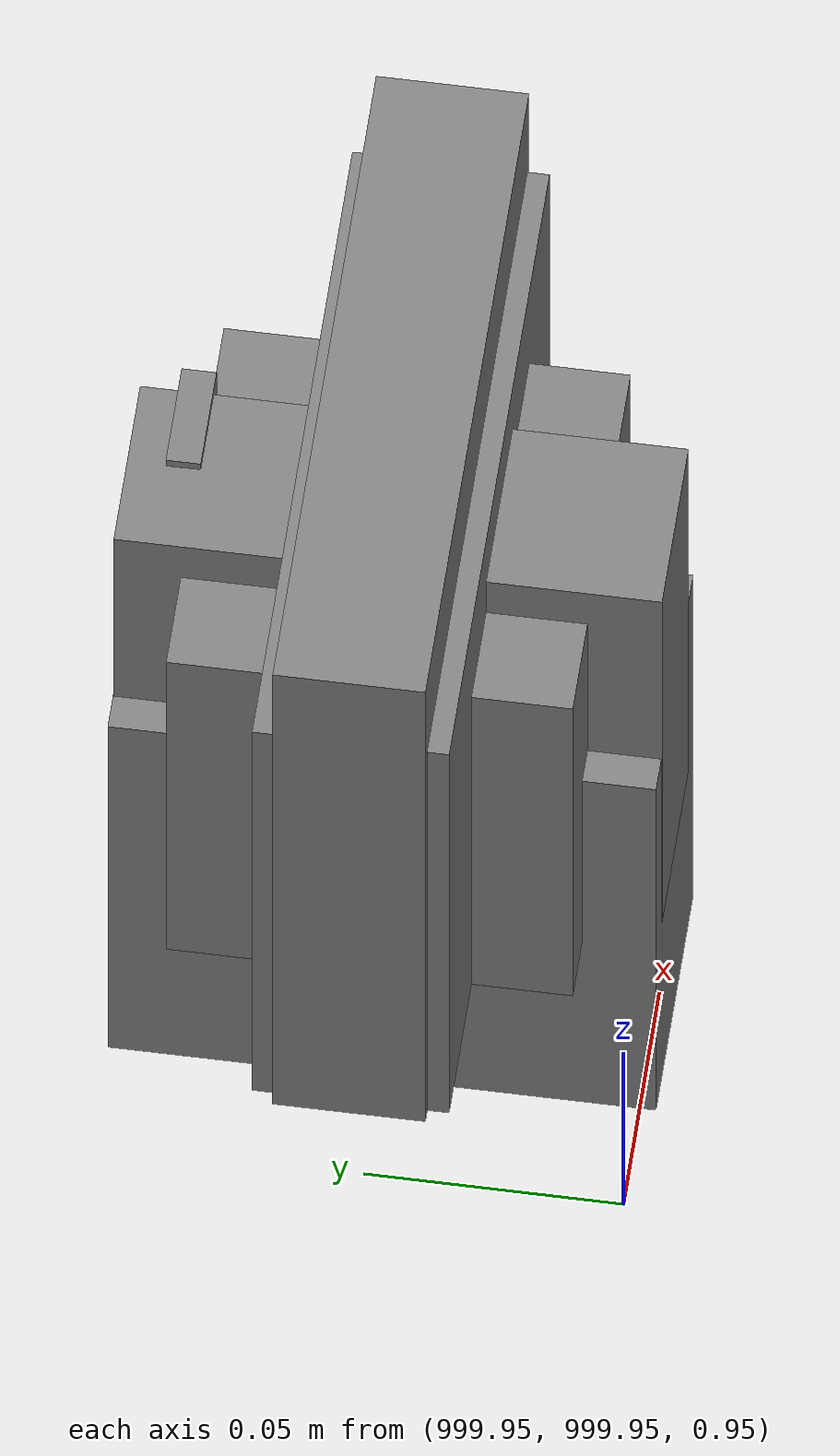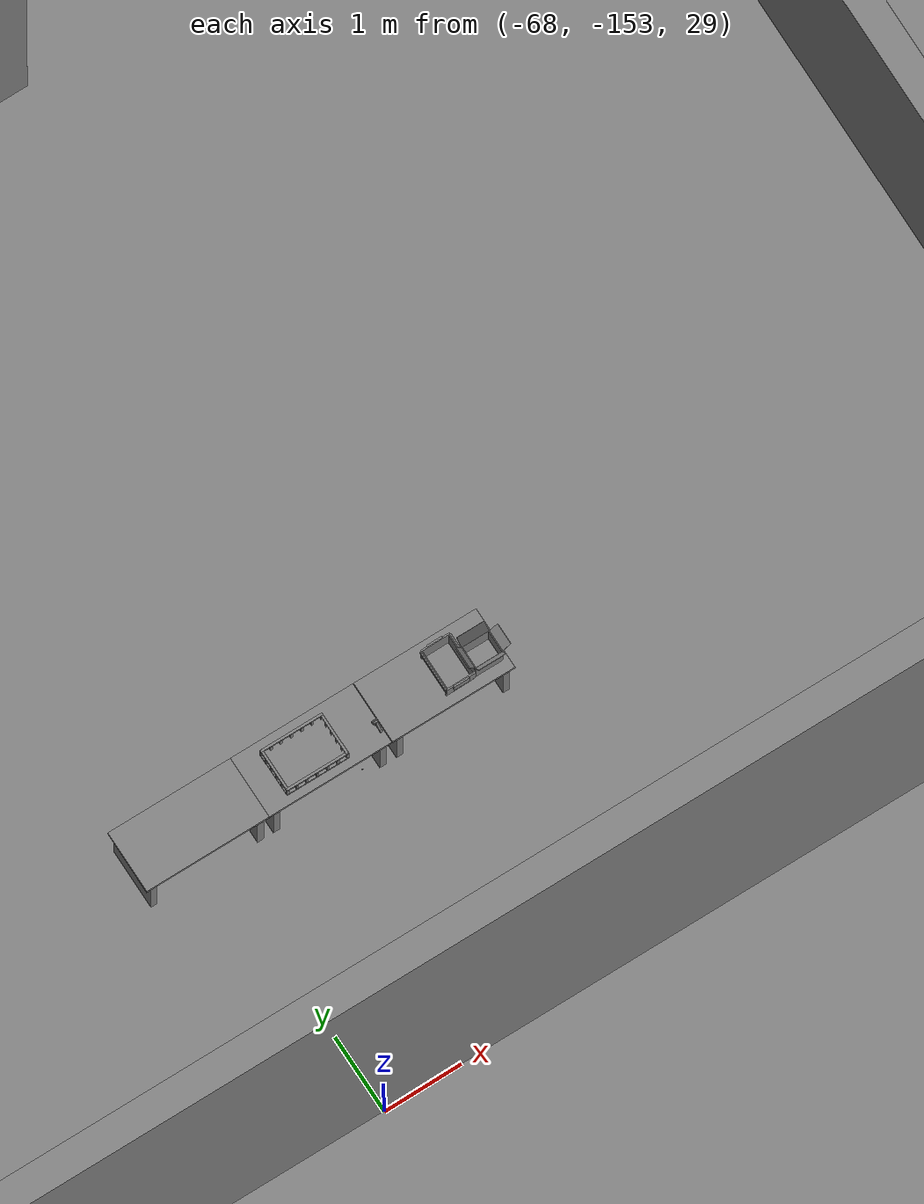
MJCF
<mujoco>
    <option gravity="0.000000000 0.000000000 -9.810000420" timestep="0.0049999999" integrator="implicitfast" density="1.225" viscosity="1.8000001e-05" noslip_iterations="10" iterations="100" sdf_iterations="50">
        <flag multiccd="disable"/>
    </option>
    <size memory="1000M"/>
    <compiler coordinate="local"/>
    <worldbody>
        <light cutoff="30" pos="0 1 1" dir="0 -1 -2"/>
        <light cutoff="30" pos="0 -1 1" dir="0 1 -2"/>
        <body pos="-64.866622925 -149.383972168 30.183746338" euler="89.999984741 89.999946594 0.000000000" name="openloong_gripper_2f85_fix_base_usda_bluebox_01">
            <geom contype="1" conaffinity="1" density="1000" type="box" material="" rgba="0.500000000 0.500000000 0.500000000 1.000000000" solimp="0.899999976 0.949999988 0.001000000" friction="1.000000000 0.005000000 0.000100000" solref="0.020000000 1.000000000" margin="0" condim="3" group="0" pos="0.276580811 0.187225342 0.000068665" quat="0.707106948 0.000077471 0.707106352 0.000077486" size="0.100000001 0.057999998 0.010000000" name="openloong_gripper_2f85_fix_base_usda_geom_4FE267A5_D370_49C2_A9F4_991484508127"/>
            <geom contype="1" conaffinity="1" density="1000" type="box" material="" rgba="0.500000000 0.500000000 0.500000000 1.000000000" solimp="0.899999976 0.949999988 0.001000000" friction="1.000000000 0.005000000 0.000100000" solref="0.020000000 1.000000000" margin="0" condim="3" group="0" pos="0.000000000 0.002883911 0.000000000" quat="0.999999881 0.000000000 0.000000000 0.000000000" size="0.254000008 0.003000000 0.172000006" name="openloong_gripper_2f85_fix_base_usda_geom_02F1D25F_7766_439E_A976_86844520AB4D"/>
            <geom contype="1" conaffinity="1" density="1000" type="box" material="" rgba="0.500000000 0.500000000 0.500000000 1.000000000" solimp="0.899999976 0.949999988 0.001000000" friction="1.000000000 0.005000000 0.000100000" solref="0.020000000 1.000000000" margin="0" condim="3" group="0" pos="0.000000000 0.124874115 0.173484802" quat="0.999796331 0.020176515 -0.000000015 0.000000030" size="0.259999990 0.119999997 0.007000000" name="openloong_gripper_2f85_fix_base_usda_geom_C5FA73A4_9E53_428C_9557_EB90D6464A80"/>
            <geom contype="1" conaffinity="1" density="1000" type="box" material="" rgba="0.500000000 0.500000000 0.500000000 1.000000000" solimp="0.899999976 0.949999988 0.001000000" friction="1.000000000 0.005000000 0.000100000" solref="0.020000000 1.000000000" margin="0" condim="3" group="0" pos="0.000000000 0.124874115 -0.173469543" quat="0.999796331 -0.020176545 -0.000000015 0.000000000" size="0.259999990 0.119999997 0.007000000" name="openloong_gripper_2f85_fix_base_usda_geom_92EBD4C1_89AC_4092_91C1_286CE5825BBD"/>
            <geom contype="1" conaffinity="1" density="1000" type="box" material="" rgba="0.500000000 0.500000000 0.500000000 1.000000000" solimp="0.899999976 0.949999988 0.001000000" friction="1.000000000 0.005000000 0.000100000" solref="0.020000000 1.000000000" margin="0" condim="3" group="0" pos="0.000000000 0.214008331 0.188980103" quat="0.999912977 0.013176724 0.000000015 0.000000000" size="0.259999990 0.029999999 0.012500000" name="openloong_gripper_2f85_fix_base_usda_geom_6C1D1D2E_252C_4688_AD2B_FFAB6347AF79"/>
            <geom contype="1" conaffinity="1" density="1000" type="box" material="" rgba="0.500000000 0.500000000 0.500000000 1.000000000" solimp="0.899999976 0.949999988 0.001000000" friction="1.000000000 0.005000000 0.000100000" solref="0.020000000 1.000000000" margin="0" condim="3" group="0" pos="-0.258361816 0.125289917 0.001876831" quat="0.702796936 -0.020792112 0.710783124 0.020769298" size="0.189999998 0.119999997 0.009000000" name="openloong_gripper_2f85_fix_base_usda_geom_2E0397C6_6DAE_4549_9D0B_CA14CE48340E"/>
            <geom contype="1" conaffinity="1" density="1000" type="box" material="" rgba="0.500000000 0.500000000 0.500000000 1.000000000" solimp="0.899999976 0.949999988 0.001000000" friction="1.000000000 0.005000000 0.000100000" solref="0.020000000 1.000000000" margin="0" condim="3" group="0" pos="0.000000000 0.214008331 -0.188980103" quat="0.999912977 -0.013176769 0.000000030 0.000000015" size="0.259999990 0.029999999 0.012500000" name="openloong_gripper_2f85_fix_base_usda_geom_C0C965E7_6A43_40C2_92BF_DA7935FBE18A"/>
            <geom contype="1" conaffinity="1" density="1000" type="box" material="" rgba="0.500000000 0.500000000 0.500000000 1.000000000" solimp="0.899999976 0.949999988 0.001000000" friction="1.000000000 0.005000000 0.000100000" solref="0.020000000 1.000000000" margin="0" condim="3" group="0" pos="-0.276611328 0.187225342 0.000068665" quat="0.707106650 0.000077441 0.707106709 0.000077456" size="0.100000001 0.057999998 0.010000000" name="openloong_gripper_2f85_fix_base_usda_geom_00D50FEA_F87B_428B_8A2B_F3A2A66B680E"/>
            <geom contype="1" conaffinity="1" density="1000" type="box" material="" rgba="0.500000000 0.500000000 0.500000000 1.000000000" solimp="0.899999976 0.949999988 0.001000000" friction="1.000000000 0.005000000 0.000100000" solref="0.020000000 1.000000000" margin="0" condim="3" group="0" pos="0.258331299 0.125289917 0.001876831" quat="0.702851415 0.018856421 0.710823774 -0.019329369" size="0.189999998 0.119999997 0.009000000" name="openloong_gripper_2f85_fix_base_usda_geom_37C28137_E8BD_4B17_8124_3A37B93DE121"/>
            <freejoint name="openloong_gripper_2f85_fix_base_usda_bluebox_01_joint"/>
            <site size="0.005000000 0.005000000 0.005000000" rgba="0.500000000 0.500000000 0.500000000 1.000000000" pos="0.000000000 0.000000000 0.000000000" quat="0.999961913 0.008726534 0.000000000 0.000000000" group="0" type="sphere" name="openloong_gripper_2f85_fix_base_usda_bluebox_01site"/>
        </body>
        <body pos="-64.496299744 -149.491867065 30.235729218" euler="0.000000000 0.000000000 89.999946594" name="openloong_gripper_2f85_fix_base_usda_cardboardbox_01">
            <geom contype="1" conaffinity="1" density="1000" type="box" material="" rgba="0.500000000 0.500000000 0.500000000 1.000000000" solimp="0.899999976 0.949999988 0.001000000" friction="1.000000000 0.005000000 0.000100000" solref="0.020000000 1.000000000" margin="0" condim="3" group="0" pos="-0.003166199 -0.004086494 0.005052090" quat="1.000000000 0.000000000 0.000000000 0.000000000" size="0.142499998 0.177500010 0.005000000" name="openloong_gripper_2f85_fix_base_usda_geom_C7ED756D_C8A7_476B_8226_3E1662BFE224"/>
            <geom contype="1" conaffinity="1" density="1000" type="box" material="" rgba="0.500000000 0.500000000 0.500000000 1.000000000" solimp="0.899999976 0.949999988 0.001000000" friction="1.000000000 0.005000000 0.000100000" solref="0.020000000 1.000000000" margin="0" condim="3" group="0" pos="-0.003166199 0.170316696 0.150570869" quat="1.000000000 0.000000000 0.000000000 0.000000000" size="0.142499998 0.005000000 0.149999991" name="openloong_gripper_2f85_fix_base_usda_geom_07300DC5_C44D_496B_B25A_FFE8997DF186"/>
            <geom contype="1" conaffinity="1" density="1000" type="box" material="" rgba="0.500000000 0.500000000 0.500000000 1.000000000" solimp="0.899999976 0.949999988 0.001000000" friction="1.000000000 0.005000000 0.000100000" solref="0.020000000 1.000000000" margin="0" condim="3" group="0" pos="-0.147399902 -0.005307198 0.150570869" quat="1.000000000 0.000000000 0.000000000 0.000000000" size="0.005000000 0.177500010 0.149999991" name="openloong_gripper_2f85_fix_base_usda_geom_BB6CA44A_081B_4CDC_9BBC_09EBBD2BE298"/>
            <geom contype="1" conaffinity="1" density="1000" type="box" material="" rgba="0.500000000 0.500000000 0.500000000 1.000000000" solimp="0.899999976 0.949999988 0.001000000" friction="1.000000000 0.005000000 0.000100000" solref="0.020000000 1.000000000" margin="0" condim="3" group="0" pos="0.140275955 -0.005307198 0.150570869" quat="1.000000000 0.000000000 0.000000000 0.000000000" size="0.005000000 0.177500010 0.149999991" name="openloong_gripper_2f85_fix_base_usda_geom_7C97EA97_A801_4DF3_A799_D6796DCFFA25"/>
            <geom contype="1" conaffinity="1" density="1000" type="box" material="" rgba="0.500000000 0.500000000 0.500000000 1.000000000" solimp="0.899999976 0.949999988 0.001000000" friction="1.000000000 0.005000000 0.000100000" solref="0.020000000 1.000000000" margin="0" condim="3" group="0" pos="-0.003166199 -0.181550980 0.150570869" quat="1.000000000 0.000000000 0.000000000 0.000000000" size="0.142499998 0.005000000 0.149999991" name="openloong_gripper_2f85_fix_base_usda_geom_EAB7B002_2D0D_471A_956B_8B437CF22670"/>
            <freejoint name="openloong_gripper_2f85_fix_base_usda_cardboardbox_01_joint"/>
            <site size="0.005000000 0.005000000 0.005000000" rgba="0.500000000 0.500000000 0.500000000 1.000000000" pos="0.000000000 0.000000000 0.000000000" quat="0.999961913 0.008726535 0.000000000 0.000000000" group="0" type="sphere" name="openloong_gripper_2f85_fix_base_usda_site_608D36C0_1DBC_4BF7_A2C2_E2F64070DC48"/>
            <body pos="0.139160156 -0.004048347 0.301930904" euler="-179.999954224 49.383502960 179.999954224" name="openloong_gripper_2f85_fix_base_usda_A1_006">
                <geom contype="1" conaffinity="1" density="1000" type="box" material="" rgba="0.500000000 0.500000000 0.500000000 1.000000000" solimp="0.899999976 0.949999988 0.001000000" friction="1.000000000 0.005000000 0.000100000" solref="0.020000000 1.000000000" margin="0" condim="3" group="0" pos="-0.071587563 0.000009537 0.001745224" quat="0.999999881 0.000000000 0.000000000 0.000000000" size="0.071249999 0.179999992 0.002500000" name="openloong_gripper_2f85_fix_base_usda_geom_62649058_4C48_4ECC_85CA_258B065E8A62"/>
                <joint armature="0" stiffness="0.07" damping="0.0099999998" axis="0.000000 1.000000 0.000000" type="hinge" name="openloong_gripper_2f85_fix_base_usda_A1_006"/>
            </body>
            <body pos="-0.145902634 -0.004086494 0.301938057" euler="-180.000000000 -60.000011444 -180.000000000" name="openloong_gripper_2f85_fix_base_usda_A2_006">
                <geom contype="1" conaffinity="1" density="1000" type="box" material="" rgba="0.500000000 0.500000000 0.500000000 1.000000000" solimp="0.899999976 0.949999988 0.001000000" friction="1.000000000 0.005000000 0.000100000" solref="0.020000000 1.000000000" margin="0" condim="3" group="0" pos="0.071268082 0.000009537 0.002717972" quat="0.000002921 0.000000000 -0.000000030 0.999999881" size="0.071249999 0.179999992 0.002500000" name="openloong_gripper_2f85_fix_base_usda_geom_DABD8436_209B_4851_8E02_DB9D49720745"/>
                <joint armature="0" stiffness="0.07" damping="0.0099999998" axis="0.000000 1.000000 0.000000" type="hinge" name="openloong_gripper_2f85_fix_base_usda_A2_006"/>
            </body>
            <body pos="-0.003385544 0.175991058 0.301930904" euler="-125.858116150 -0.000004561 0.000002331" name="openloong_gripper_2f85_fix_base_usda_B2_006">
                <geom contype="1" conaffinity="1" density="1000" type="box" material="" rgba="0.500000000 0.500000000 0.500000000 1.000000000" solimp="0.899999976 0.949999988 0.001000000" friction="1.000000000 0.005000000 0.000100000" solref="0.020000000 1.000000000" margin="0" condim="3" group="0" pos="0.000009537 -0.070939064 -0.002470016" quat="0.999614120 0.027776197 -0.000000015 0.000000030" size="0.137500003 0.064999998 0.005000000" name="openloong_gripper_2f85_fix_base_usda_geom_4157E42B_65F3_4000_8D82_C9C73F343110"/>
                <joint armature="0" stiffness="0.07" damping="0.0099999998" axis="1.000000 0.000000 0.000000" type="hinge" name="openloong_gripper_2f85_fix_base_usda_B2_006"/>
            </body>
            <body pos="-0.003385544 -0.184140205 0.301938057" euler="147.805557251 0.000000000 0.000000000" name="openloong_gripper_2f85_fix_base_usda_B1_006">
                <geom contype="1" conaffinity="1" density="1000" type="box" material="" rgba="0.500000000 0.500000000 0.500000000 1.000000000" solimp="0.899999976 0.949999988 0.001000000" friction="1.000000000 0.005000000 0.000100000" solref="0.020000000 1.000000000" margin="0" condim="3" group="0" pos="-0.000028610 0.070202351 -0.002703667" quat="0.999614179 -0.027776167 0.000000000 0.000000000" size="0.137500003 0.064999998 0.005000000" name="openloong_gripper_2f85_fix_base_usda_geom_D5043D45_A4A4_4D59_A12B_15AECBFE3E7B"/>
                <joint armature="0" stiffness="0.07" damping="0.0099999998" axis="1.000000 0.000000 0.000000" type="hinge" name="openloong_gripper_2f85_fix_base_usda_B1_006"/>
            </body>
        </body>
        <body pos="-65.882858276 -149.481979370 30.229999542" euler="-64.487716675 0.000000000 0.000000000" name="openloong_gripper_2f85_fix_base_usda_Barcode">
            <geom contype="1" conaffinity="1" density="1000" type="box" material="" rgba="0.500000000 0.500000000 0.500000000 1.000000000" solimp="0.899999976 0.949999988 0.001000000" friction="1.000000000 0.005000000 0.000100000" solref="0.020000000 1.000000000" margin="0" condim="3" group="0" pos="0.000000000 0.013038635 0.001419067" quat="0.000000000 0.000000000 0.000000000 1.000000119" size="0.034000002 0.010000000 0.017999999" name="openloong_gripper_2f85_fix_base_usda_geom_F16BCCEC_B27E_4B71_85D1_228A9C1CA4B0"/>
            <geom contype="1" conaffinity="1" density="1000" type="box" material="" rgba="0.500000000 0.500000000 0.500000000 1.000000000" solimp="0.899999976 0.949999988 0.001000000" friction="1.000000000 0.005000000 0.000100000" solref="0.020000000 1.000000000" margin="0" condim="3" group="0" pos="0.000000000 -0.035301208 -0.007095337" quat="0.000000000 0.000000000 -0.043619365 0.999048233" size="0.028999999 0.010000000 0.020000000" name="openloong_gripper_2f85_fix_base_usda_geom_36F5A1C6_7E30_48D1_9FEF_76D709A55FCE"/>
            <geom contype="1" conaffinity="1" density="1000" type="box" material="" rgba="0.500000000 0.500000000 0.500000000 1.000000000" solimp="0.899999976 0.949999988 0.001000000" friction="1.000000000 0.005000000 0.000100000" solref="0.020000000 1.000000000" margin="0" condim="3" group="0" pos="0.000000000 -0.043411255 -0.011749268" quat="0.922262907 0.386563420 0.000000000 0.000000000" size="0.026000001 0.010000000 0.020000000" name="openloong_gripper_2f85_fix_base_usda_geom_9231046A_1255_431D_87D2_1B3C636E3B77"/>
            <geom contype="1" conaffinity="1" density="1000" type="box" material="" rgba="0.500000000 0.500000000 0.500000000 1.000000000" solimp="0.899999976 0.949999988 0.001000000" friction="1.000000000 0.005000000 0.000100000" solref="0.020000000 1.000000000" margin="0" condim="3" group="0" pos="0.000000000 -0.016967773 -0.031860352" quat="0.000000000 0.000000000 0.000000000 1.000000119" size="0.008000000 0.010000000 0.013000000" name="openloong_gripper_2f85_fix_base_usda_geom_1D4FB693_FA84_4DF8_A661_13D53CA9FDD0"/>
            <geom contype="1" conaffinity="1" density="1000" type="box" material="" rgba="0.500000000 0.500000000 0.500000000 1.000000000" solimp="0.899999976 0.949999988 0.001000000" friction="1.000000000 0.005000000 0.000100000" solref="0.020000000 1.000000000" margin="0" condim="3" group="0" pos="0.000000000 -0.001869202 0.000312805" quat="0.953716993 0.300705761 0.000000000 0.000000000" size="0.032000002 0.010000000 0.018999999" name="openloong_gripper_2f85_fix_base_usda_geom_C528DC70_09A1_4BFB_BEAB_BE89852B2D60"/>
            <geom contype="1" conaffinity="1" density="1000" type="box" material="" rgba="0.500000000 0.500000000 0.500000000 1.000000000" solimp="0.899999976 0.949999988 0.001000000" friction="1.000000000 0.005000000 0.000100000" solref="0.020000000 1.000000000" margin="0" condim="3" group="0" pos="0.000000000 -0.019531250 -0.003173828" quat="0.953716993 0.300705761 0.000000000 0.000000000" size="0.030999999 0.010000000 0.020000000" name="openloong_gripper_2f85_fix_base_usda_geom_CB344734_FE51_457F_A950_781F86774D00"/>
            <geom contype="1" conaffinity="1" density="1000" type="box" material="" rgba="0.500000000 0.500000000 0.500000000 1.000000000" solimp="0.899999976 0.949999988 0.001000000" friction="1.000000000 0.005000000 0.000100000" solref="0.020000000 1.000000000" margin="0" condim="3" group="0" pos="0.000000000 -0.035301208 -0.007095337" quat="0.953716993 0.300705761 0.000000000 0.000000000" size="0.028999999 0.010000000 0.020000000" name="openloong_gripper_2f85_fix_base_usda_geom_AE8AD059_F674_403E_A3C4_DBBDD5398784"/>
            <geom contype="1" conaffinity="1" density="1000" type="box" material="" rgba="0.500000000 0.500000000 0.500000000 1.000000000" solimp="0.899999976 0.949999988 0.001000000" friction="1.000000000 0.005000000 0.000100000" solref="0.020000000 1.000000000" margin="0" condim="3" group="0" pos="0.000000000 -0.042617798 -0.071121216" quat="0.000000000 0.000000000 0.000000000 1.000000119" size="0.013000000 0.021000000 0.059999999" name="openloong_gripper_2f85_fix_base_usda_geom_5747ACC9_2F99_4DA4_A6CA_249E9392C72E"/>
            <freejoint name="openloong_gripper_2f85_fix_base_usda_Barcode_joint"/>
            <site size="0.005000000 0.005000000 0.005000000" rgba="0.500000000 0.500000000 0.500000000 1.000000000" pos="0.000000000 0.000000000 0.000000000" quat="1.000000000 0.000000000 0.000000000 0.000000000" group="0" type="sphere" name="openloong_gripper_2f85_fix_base_usda_Barcode_site"/>
        </body>
        <body pos="-66.745018005 -149.392349243 30.184000015" euler="0.000000000 0.000000000 89.999946594" name="[22331793371936]_Basket_01">
            <geom contype="1" conaffinity="1" density="1000" type="box" material="" rgba="0.500000000 0.500000000 0.500000000 1.000000000" solimp="0.899999976 0.949999988 0.001000000" friction="1.000000000 0.005000000 0.000100000" solref="0.020000000 1.000000000" margin="0" condim="3" group="0" pos="-0.052425385 0.389207840 0.089787483" quat="0.707107008 0.000000000 0.000000000 0.707106411" size="0.014249999 0.014249999 0.059999999" name="[22331793371936]_geom_96A53573_F0D8_46C7_9479_BA789972A987"/>
            <geom contype="1" conaffinity="1" density="1000" type="box" material="" rgba="0.500000000 0.500000000 0.500000000 1.000000000" solimp="0.899999976 0.949999988 0.001000000" friction="1.000000000 0.005000000 0.000100000" solref="0.020000000 1.000000000" margin="0" condim="3" group="0" pos="0.264015198 -0.133043289 0.089787483" quat="0.707107008 0.000000000 0.000000000 0.707106411" size="0.014249999 0.014249999 0.059999999" name="[22331793371936]_geom_D73F55E4_84E3_4588_B4AB_431A83D18BD9"/>
            <geom contype="1" conaffinity="1" density="1000" type="box" material="" rgba="0.500000000 0.500000000 0.500000000 1.000000000" solimp="0.899999976 0.949999988 0.001000000" friction="1.000000000 0.005000000 0.000100000" solref="0.020000000 1.000000000" margin="0" condim="3" group="0" pos="-0.264015198 -0.265548706 0.089793205" quat="0.707107008 0.000000000 0.000000000 0.707106411" size="0.014249999 0.014249999 0.059999999" name="[22331793371936]_geom_FFAD2FBB_29C5_495B_91ED_6F5C0BEF8558"/>
            <geom contype="1" conaffinity="1" density="1000" type="box" material="" rgba="0.500000000 0.500000000 0.500000000 1.000000000" solimp="0.899999976 0.949999988 0.001000000" friction="1.000000000 0.005000000 0.000100000" solref="0.020000000 1.000000000" margin="0" condim="3" group="0" pos="-0.160263062 -0.389322281 0.089793205" quat="0.707107008 0.000000000 0.000000000 0.707106411" size="0.014249999 0.014249999 0.059999999" name="[22331793371936]_geom_C938B42A_2C1C_45EA_A4C4_C3571F26C44E"/>
            <geom contype="1" conaffinity="1" density="1000" type="box" material="" rgba="0.500000000 0.500000000 0.500000000 1.000000000" solimp="0.899999976 0.949999988 0.001000000" friction="1.000000000 0.005000000 0.000100000" solref="0.020000000 1.000000000" margin="0" condim="3" group="0" pos="0.162265778 -0.389322281 0.089787483" quat="0.707107008 0.000000000 0.000000000 0.707106411" size="0.014249999 0.014249999 0.059999999" name="[22331793371936]_geom_99B80B7C_A64A_4620_8EC8_F871CCC8F189"/>
            <geom contype="1" conaffinity="1" density="1000" type="box" material="" rgba="0.500000000 0.500000000 0.500000000 1.000000000" solimp="0.899999976 0.949999988 0.001000000" friction="1.000000000 0.005000000 0.000100000" solref="0.020000000 1.000000000" margin="0" condim="3" group="0" pos="0.264015198 0.389207840 0.089787483" quat="0.707107008 0.000000000 0.000000000 0.707106411" size="0.014249999 0.014249999 0.059999999" name="[22331793371936]_geom_0B4F08E2_7FDC_4E48_B3B9_CE80C44D87A8"/>
            <geom contype="1" conaffinity="1" density="1000" type="box" material="" rgba="0.500000000 0.500000000 0.500000000 1.000000000" solimp="0.899999976 0.949999988 0.001000000" friction="1.000000000 0.005000000 0.000100000" solref="0.020000000 1.000000000" margin="0" condim="3" group="0" pos="-0.264015198 -0.133043289 0.089793205" quat="0.707107008 0.000000000 0.000000000 0.707106411" size="0.014249999 0.014249999 0.059999999" name="[22331793371936]_geom_C1E7F8DA_7C41_460E_91C1_090022C8D25D"/>
            <geom contype="1" conaffinity="1" density="1000" type="box" material="" rgba="0.500000000 0.500000000 0.500000000 1.000000000" solimp="0.899999976 0.949999988 0.001000000" friction="1.000000000 0.005000000 0.000100000" solref="0.020000000 1.000000000" margin="0" condim="3" group="0" pos="-0.264026642 0.269256592 0.089793205" quat="0.707107008 0.000000000 0.000000000 0.707106411" size="0.014249999 0.014249999 0.059999999" name="[22331793371936]_geom_9A130758_5127_4A17_9CBF_6BDCF6E47FA3"/>
            <geom contype="1" conaffinity="1" density="1000" type="box" material="" rgba="0.500000000 0.500000000 0.500000000 1.000000000" solimp="0.899999976 0.949999988 0.001000000" friction="1.000000000 0.005000000 0.000100000" solref="0.020000000 1.000000000" margin="0" condim="3" group="0" pos="0.054462433 0.389207840 0.089787483" quat="0.707107008 0.000000000 0.000000000 0.707106411" size="0.014249999 0.014249999 0.059999999" name="[22331793371936]_geom_0E33078C_589A_408A_993D_A344CBD35E11"/>
            <geom contype="1" conaffinity="1" density="1000" type="box" material="" rgba="0.500000000 0.500000000 0.500000000 1.000000000" solimp="0.899999976 0.949999988 0.001000000" friction="1.000000000 0.005000000 0.000100000" solref="0.020000000 1.000000000" margin="0" condim="3" group="0" pos="0.054462433 -0.389322281 0.089787483" quat="0.707107008 0.000000000 0.000000000 0.707106411" size="0.014249999 0.014249999 0.059999999" name="[22331793371936]_geom_51D09915_1DDC_42A8_A48C_9096B35E63B4"/>
            <geom contype="1" conaffinity="1" density="1000" type="box" material="" rgba="0.500000000 0.500000000 0.500000000 1.000000000" solimp="0.899999976 0.949999988 0.001000000" friction="1.000000000 0.005000000 0.000100000" solref="0.020000000 1.000000000" margin="0" condim="3" group="0" pos="0.264015198 0.269256592 0.089793205" quat="0.707107008 0.000000000 0.000000000 0.707106411" size="0.014249999 0.014249999 0.059999999" name="[22331793371936]_geom_EBC7B9C5_1B40_48D9_B2DA_7AA63629D8D9"/>
            <geom contype="1" conaffinity="1" density="1000" type="box" material="" rgba="0.500000000 0.500000000 0.500000000 1.000000000" solimp="0.899999976 0.949999988 0.001000000" friction="1.000000000 0.005000000 0.000100000" solref="0.020000000 1.000000000" margin="0" condim="3" group="0" pos="0.264015198 -0.389322281 0.089787483" quat="0.707107008 0.000000000 0.000000000 0.707106411" size="0.014249999 0.014249999 0.059999999" name="[22331793371936]_geom_16237BB4_40DB_4C49_BBA5_DEE4EE941332"/>
            <geom contype="1" conaffinity="1" density="1000" type="box" material="" rgba="0.500000000 0.500000000 0.500000000 1.000000000" solimp="0.899999976 0.949999988 0.001000000" friction="1.000000000 0.005000000 0.000100000" solref="0.020000000 1.000000000" margin="0" condim="3" group="0" pos="0.000000000 0.000000000 0.015998840" quat="0.707107008 0.000000000 0.000000000 0.707106411" size="0.403499991 0.279000014 0.015750000" name="[22331793371936]_geom_D814AD31_4458_4628_903E_A8EBAC8F8688"/>
            <geom contype="1" conaffinity="1" density="1000" type="box" material="" rgba="0.500000000 0.500000000 0.500000000 1.000000000" solimp="0.899999976 0.949999988 0.001000000" friction="1.000000000 0.005000000 0.000100000" solref="0.020000000 1.000000000" margin="0" condim="3" group="0" pos="0.000000000 -0.389476776 0.163619041" quat="0.707107008 0.000000000 0.000000000 0.707106411" size="0.015000000 0.277500004 0.015750000" name="[22331793371936]_geom_0F841DBE_97E6_4798_BFD5_12DA30D377BE"/>
            <geom contype="1" conaffinity="1" density="1000" type="box" material="" rgba="0.500000000 0.500000000 0.500000000 1.000000000" solimp="0.899999976 0.949999988 0.001000000" friction="1.000000000 0.005000000 0.000100000" solref="0.020000000 1.000000000" margin="0" condim="3" group="0" pos="0.162265778 0.389207840 0.089787483" quat="0.707107008 0.000000000 0.000000000 0.707106411" size="0.014249999 0.014249999 0.059999999" name="[22331793371936]_geom_65B00E20_7547_425E_A520_A2CB4E3813F2"/>
            <geom contype="1" conaffinity="1" density="1000" type="box" material="" rgba="0.500000000 0.500000000 0.500000000 1.000000000" solimp="0.899999976 0.949999988 0.001000000" friction="1.000000000 0.005000000 0.000100000" solref="0.020000000 1.000000000" margin="0" condim="3" group="0" pos="0.000000000 0.389471054 0.163619041" quat="0.707107008 0.000000000 0.000000000 0.707106411" size="0.015000000 0.277500004 0.015750000" name="[22331793371936]_geom_2B75DBBE_6B17_47F0_B7DD_60C428E75C32"/>
            <geom contype="1" conaffinity="1" density="1000" type="box" material="" rgba="0.500000000 0.500000000 0.500000000 1.000000000" solimp="0.899999976 0.949999988 0.001000000" friction="1.000000000 0.005000000 0.000100000" solref="0.020000000 1.000000000" margin="0" condim="3" group="0" pos="-0.263511658 0.000000000 0.163619041" quat="0.707107008 0.000000000 0.000000000 0.707106411" size="0.403499991 0.015000000 0.015750000" name="[22331793371936]_geom_F99A32F4_71CF_4C79_8ED2_A95172D51822"/>
            <geom contype="1" conaffinity="1" density="1000" type="box" material="" rgba="0.500000000 0.500000000 0.500000000 1.000000000" solimp="0.899999976 0.949999988 0.001000000" friction="1.000000000 0.005000000 0.000100000" solref="0.020000000 1.000000000" margin="0" condim="3" group="0" pos="-0.264015198 0.141334534 0.089793205" quat="0.707107008 0.000000000 0.000000000 0.707106411" size="0.014249999 0.014249999 0.059999999" name="[22331793371936]_geom_DA388D25_4FB9_4520_8463_4A33140E3137"/>
            <geom contype="1" conaffinity="1" density="1000" type="box" material="" rgba="0.500000000 0.500000000 0.500000000 1.000000000" solimp="0.899999976 0.949999988 0.001000000" friction="1.000000000 0.005000000 0.000100000" solref="0.020000000 1.000000000" margin="0" condim="3" group="0" pos="0.264015198 -0.265548706 0.089787483" quat="0.707107008 0.000000000 0.000000000 0.707106411" size="0.014249999 0.014249999 0.059999999" name="[22331793371936]_geom_C3E91A6A_807E_4EE6_B44A_A885716F7D14"/>
            <geom contype="1" conaffinity="1" density="1000" type="box" material="" rgba="0.500000000 0.500000000 0.500000000 1.000000000" solimp="0.899999976 0.949999988 0.001000000" friction="1.000000000 0.005000000 0.000100000" solref="0.020000000 1.000000000" margin="0" condim="3" group="0" pos="-0.160263062 0.389207840 0.089787483" quat="0.707107008 0.000000000 0.000000000 0.707106411" size="0.014249999 0.014249999 0.059999999" name="[22331793371936]_geom_D2E83FE6_6888_40F4_8587_8C5787E0C0EC"/>
            <geom contype="1" conaffinity="1" density="1000" type="box" material="" rgba="0.500000000 0.500000000 0.500000000 1.000000000" solimp="0.899999976 0.949999988 0.001000000" friction="1.000000000 0.005000000 0.000100000" solref="0.020000000 1.000000000" margin="0" condim="3" group="0" pos="-0.052425385 -0.389322281 0.089787483" quat="0.707107008 0.000000000 0.000000000 0.707106411" size="0.014249999 0.014249999 0.059999999" name="[22331793371936]_geom_77616443_2F85_42D7_A4F1_984074D4DA73"/>
            <geom contype="1" conaffinity="1" density="1000" type="box" material="" rgba="0.500000000 0.500000000 0.500000000 1.000000000" solimp="0.899999976 0.949999988 0.001000000" friction="1.000000000 0.005000000 0.000100000" solref="0.020000000 1.000000000" margin="0" condim="3" group="0" pos="-0.264026642 -0.389322281 0.089793205" quat="0.707107008 0.000000000 0.000000000 0.707106411" size="0.014249999 0.014249999 0.059999999" name="[22331793371936]_geom_D0F566C9_E270_410D_8E66_B8611EB494B4"/>
            <geom contype="1" conaffinity="1" density="1000" type="box" material="" rgba="0.500000000 0.500000000 0.500000000 1.000000000" solimp="0.899999976 0.949999988 0.001000000" friction="1.000000000 0.005000000 0.000100000" solref="0.020000000 1.000000000" margin="0" condim="3" group="0" pos="0.264015198 0.141334534 0.089787483" quat="0.707107008 0.000000000 0.000000000 0.707106411" size="0.014249999 0.014249999 0.059999999" name="[22331793371936]_geom_ECB0B1E0_8D04_4A1F_A6F6_0D93204F3300"/>
            <geom contype="1" conaffinity="1" density="1000" type="box" material="" rgba="0.500000000 0.500000000 0.500000000 1.000000000" solimp="0.899999976 0.949999988 0.001000000" friction="1.000000000 0.005000000 0.000100000" solref="0.020000000 1.000000000" margin="0" condim="3" group="0" pos="-0.264015198 0.389207840 0.089793205" quat="0.707107008 0.000000000 0.000000000 0.707106411" size="0.014249999 0.014249999 0.059999999" name="[22331793371936]_geom_4B831B55_AAA4_4FDA_9519_B01B94C732FF"/>
            <geom contype="1" conaffinity="1" density="1000" type="box" material="" rgba="0.500000000 0.500000000 0.500000000 1.000000000" solimp="0.899999976 0.949999988 0.001000000" friction="1.000000000 0.005000000 0.000100000" solref="0.020000000 1.000000000" margin="0" condim="3" group="0" pos="0.264015198 0.004480362 0.089787483" quat="0.707107008 0.000000000 0.000000000 0.707106411" size="0.014249999 0.014249999 0.059999999" name="[22331793371936]_geom_220DCD5D_8093_411E_A64D_49E092981B38"/>
            <geom contype="1" conaffinity="1" density="1000" type="box" material="" rgba="0.500000000 0.500000000 0.500000000 1.000000000" solimp="0.899999976 0.949999988 0.001000000" friction="1.000000000 0.005000000 0.000100000" solref="0.020000000 1.000000000" margin="0" condim="3" group="0" pos="0.263694763 -0.000011444 0.163619041" quat="0.707107008 0.000000000 0.000000000 0.707106411" size="0.403499991 0.015000000 0.015750000" name="[22331793371936]_geom_5977EDA7_8792_4971_9549_97A2D69CB02C"/>
            <geom contype="1" conaffinity="1" density="1000" type="box" material="" rgba="0.500000000 0.500000000 0.500000000 1.000000000" solimp="0.899999976 0.949999988 0.001000000" friction="1.000000000 0.005000000 0.000100000" solref="0.020000000 1.000000000" margin="0" condim="3" group="0" pos="-0.264015198 0.004480362 0.089793205" quat="0.707107008 0.000000000 0.000000000 0.707106411" size="0.014249999 0.014249999 0.059999999" name="[22331793371936]_geom_6478C786_DF67_4F75_B0C4_E263DB84608C"/>
            <freejoint name="[22331793371936]_joint_F89C47E3_7A3F_41A0_B062_7BA51FB98D7B"/>
        </body>
        <body pos="0.000000000 0.000000000 0.000000000" euler="0.000000000 0.000000000 0.000000000" name="Static Objects_Static Objects">
            <geom contype="1" conaffinity="1" density="1000" type="box" material="" rgba="0.500000000 0.500000000 0.500000000 1.000000000" solimp="0.899999976 0.949999988 0.001000000" friction="1.000000000 0.005000000 0.000100000" solref="0.020000000 1.000000000" margin="0" condim="3" group="0" pos="-67.544113159 -149.365814209 29.727830887" quat="0.500000417 0.499999970 0.499999553 0.499999970" size="0.381000012 0.319999993 0.041000001" name="Static Objects_geom_3C918B06_EC8A_4AC8_B1DF_7721C1EC4A48"/>
            <geom contype="1" conaffinity="1" density="1000" type="box" material="" rgba="0.500000000 0.500000000 0.500000000 1.000000000" solimp="0.899999976 0.949999988 0.001000000" friction="1.000000000 0.005000000 0.000100000" solref="0.020000000 1.000000000" margin="0" condim="3" group="0" pos="-68.239501953 -149.365814209 30.086868286" quat="0.500000417 0.499999970 0.499999553 0.499999970" size="0.370999992 0.039500002 0.745000005" name="Static Objects_geom_4140A644_36D0_4B62_93EC_735DDE4E9475"/>
            <geom contype="1" conaffinity="1" density="1000" type="box" material="" rgba="0.500000000 0.500000000 0.500000000 1.000000000" solimp="0.899999976 0.949999988 0.001000000" friction="1.000000000 0.005000000 0.000100000" solref="0.020000000 1.000000000" margin="0" condim="3" group="0" pos="-68.239501953 -149.365814209 30.147235870" quat="0.500000417 0.499999970 0.499999553 0.499999970" size="0.400000006 0.022000000 0.800000012" name="Static Objects_geom_5FD74A44_C118_4585_B87B_FBB8EFF3A6AA"/>
            <geom contype="1" conaffinity="1" density="1000" type="box" material="" rgba="0.500000000 0.500000000 0.500000000 1.000000000" solimp="0.899999976 0.949999988 0.001000000" friction="1.000000000 0.005000000 0.000100000" solref="0.020000000 1.000000000" margin="0" condim="3" group="0" pos="-68.934890747 -149.365814209 29.727830887" quat="0.500000417 0.499999970 0.499999553 0.499999970" size="0.381000012 0.319999993 0.041000001" name="Static Objects_geom_F42332B0_B46D_47BA_83A2_638CD969B01D"/>
            <geom contype="1" conaffinity="1" density="1000" type="box" material="" rgba="0.500000000 0.500000000 0.500000000 1.000000000" solimp="0.899999976 0.949999988 0.001000000" friction="1.000000000 0.005000000 0.000100000" solref="0.020000000 1.000000000" margin="0" condim="3" group="0" pos="-68.239501953 -149.365814209 29.561563492" quat="0.500000417 0.499999970 0.499999553 0.499999970" size="0.020000000 0.022000000 0.660000026" name="Static Objects_geom_3DCC5DFD_69DD_48F9_B6A9_EEFFEA829EE5"/>
            <geom contype="1" conaffinity="1" density="1000" type="box" material="" rgba="0.500000000 0.500000000 0.500000000 1.000000000" solimp="0.899999976 0.949999988 0.001000000" friction="1.000000000 0.005000000 0.000100000" solref="0.020000000 1.000000000" margin="0" condim="3" group="0" pos="-65.945671082 -149.365814209 29.727830887" quat="0.500000417 0.499999970 0.499999553 0.499999970" size="0.381000012 0.319999993 0.041000001" name="Static Objects_geom_C86AA747_D09A_411D_93AE_97C3F5D3E4B9"/>
            <geom contype="1" conaffinity="1" density="1000" type="box" material="" rgba="0.500000000 0.500000000 0.500000000 1.000000000" solimp="0.899999976 0.949999988 0.001000000" friction="1.000000000 0.005000000 0.000100000" solref="0.020000000 1.000000000" margin="0" condim="3" group="0" pos="-66.641059875 -149.365814209 30.086868286" quat="0.500000417 0.499999970 0.499999553 0.499999970" size="0.370999992 0.039500002 0.745000005" name="Static Objects_geom_77FA3B11_4B37_48D8_B3D4_5E47DAAFB412"/>
            <geom contype="1" conaffinity="1" density="1000" type="box" material="" rgba="0.500000000 0.500000000 0.500000000 1.000000000" solimp="0.899999976 0.949999988 0.001000000" friction="1.000000000 0.005000000 0.000100000" solref="0.020000000 1.000000000" margin="0" condim="3" group="0" pos="-66.641059875 -149.365814209 30.147235870" quat="0.500000417 0.499999970 0.499999553 0.499999970" size="0.400000006 0.022000000 0.800000012" name="Static Objects_geom_48E00FC3_07DA_4C7C_B3EC_BA377C33C517"/>
            <geom contype="1" conaffinity="1" density="1000" type="box" material="" rgba="0.500000000 0.500000000 0.500000000 1.000000000" solimp="0.899999976 0.949999988 0.001000000" friction="1.000000000 0.005000000 0.000100000" solref="0.020000000 1.000000000" margin="0" condim="3" group="0" pos="-67.336448669 -149.365814209 29.727830887" quat="0.500000417 0.499999970 0.499999553 0.499999970" size="0.381000012 0.319999993 0.041000001" name="Static Objects_geom_058A20C1_774E_4BBF_AF22_68410B8F5E77"/>
            <geom contype="1" conaffinity="1" density="1000" type="box" material="" rgba="0.500000000 0.500000000 0.500000000 1.000000000" solimp="0.899999976 0.949999988 0.001000000" friction="1.000000000 0.005000000 0.000100000" solref="0.020000000 1.000000000" margin="0" condim="3" group="0" pos="-66.641059875 -149.365814209 29.561563492" quat="0.500000417 0.499999970 0.499999553 0.499999970" size="0.020000000 0.022000000 0.660000026" name="Static Objects_geom_BC0788F2_9247_4653_8184_BED3CAF20D2B"/>
            <geom contype="1" conaffinity="1" density="1000" type="box" material="" rgba="0.500000000 0.500000000 0.500000000 1.000000000" solimp="0.899999976 0.949999988 0.001000000" friction="1.000000000 0.005000000 0.000100000" solref="0.020000000 1.000000000" margin="0" condim="3" group="0" pos="-64.338577271 -149.365814209 29.727830887" quat="0.500000417 0.499999970 0.499999553 0.499999970" size="0.381000012 0.319999993 0.041000001" name="Static Objects_geom_045AFCC7_B01A_4B9B_8B46_344678999230"/>
            <geom contype="1" conaffinity="1" density="1000" type="box" material="" rgba="0.500000000 0.500000000 0.500000000 1.000000000" solimp="0.899999976 0.949999988 0.001000000" friction="1.000000000 0.005000000 0.000100000" solref="0.020000000 1.000000000" margin="0" condim="3" group="0" pos="-65.033966064 -149.365814209 30.086868286" quat="0.500000417 0.499999970 0.499999553 0.499999970" size="0.370999992 0.039500002 0.745000005" name="Static Objects_geom_9982099B_D9AF_43D5_B977_58D9F7BDB854"/>
            <geom contype="1" conaffinity="1" density="1000" type="box" material="" rgba="0.500000000 0.500000000 0.500000000 1.000000000" solimp="0.899999976 0.949999988 0.001000000" friction="1.000000000 0.005000000 0.000100000" solref="0.020000000 1.000000000" margin="0" condim="3" group="0" pos="-65.033966064 -149.365814209 30.147235870" quat="0.500000417 0.499999970 0.499999553 0.499999970" size="0.400000006 0.022000000 0.800000012" name="Static Objects_geom_CC333EE9_AB36_4CD4_B87E_26A8134FA394"/>
            <geom contype="1" conaffinity="1" density="1000" type="box" material="" rgba="0.500000000 0.500000000 0.500000000 1.000000000" solimp="0.899999976 0.949999988 0.001000000" friction="1.000000000 0.005000000 0.000100000" solref="0.020000000 1.000000000" margin="0" condim="3" group="0" pos="-65.729354858 -149.365814209 29.727830887" quat="0.500000417 0.499999970 0.499999553 0.499999970" size="0.381000012 0.319999993 0.041000001" name="Static Objects_geom_0E7BCEDB_1FAF_4125_B83D_4774F60F90E8"/>
            <geom contype="1" conaffinity="1" density="1000" type="box" material="" rgba="0.500000000 0.500000000 0.500000000 1.000000000" solimp="0.899999976 0.949999988 0.001000000" friction="1.000000000 0.005000000 0.000100000" solref="0.020000000 1.000000000" margin="0" condim="3" group="0" pos="-65.033966064 -149.365814209 29.561563492" quat="0.500000417 0.499999970 0.499999553 0.499999970" size="0.020000000 0.022000000 0.660000026" name="Static Objects_geom_5C77ED30_C9EE_419C_B637_7F0408B3591B"/>
            <geom contype="1" conaffinity="1" density="1000" type="box" material="" rgba="0.500000000 0.500000000 0.500000000 1.000000000" solimp="0.899999976 0.949999988 0.001000000" friction="1.000000000 0.005000000 0.000100000" solref="0.020000000 1.000000000" margin="0" condim="3" group="0" pos="-61.754566193 -137.853729248 33.906845093" quat="0.707107067 0.000000000 0.000000000 0.707106471" size="0.759999990 0.759999990 4.500000000" name="Static Objects_geom_FC9BFA63_372E_4143_8BDF_7FF2B3211930"/>
            <geom contype="1" conaffinity="1" density="1000" type="box" material="" rgba="0.500000000 0.500000000 0.500000000 1.000000000" solimp="0.899999976 0.949999988 0.001000000" friction="1.000000000 0.005000000 0.000100000" solref="0.020000000 1.000000000" margin="0" condim="3" group="0" pos="-57.511135101 -144.927108765 31.707921982" quat="1.000000000 0.000000000 0.000000000 0.000000000" size="0.200000003 8.000000000 2.299999952" name="Static Objects_geom_C9B38F2C_1387_4CF0_AC04_58EB186DEE31"/>
            <geom contype="1" conaffinity="1" density="1000" type="box" material="" rgba="0.500000000 0.500000000 0.500000000 1.000000000" solimp="0.899999976 0.949999988 0.001000000" friction="1.000000000 0.005000000 0.000100000" solref="0.020000000 1.000000000" margin="0" condim="3" group="0" pos="-80.517646790 -157.574050903 31.688196182" quat="0.707107067 0.000000000 0.000000000 0.707106471" size="0.600000024 0.600000024 2.299999952" name="Static Objects_geom_1949DDEC_1DFA_4883_B878_3F54966BBE05"/>
            <geom contype="1" conaffinity="1" density="1000" type="box" material="" rgba="0.500000000 0.500000000 0.500000000 1.000000000" solimp="0.899999976 0.949999988 0.001000000" friction="1.000000000 0.005000000 0.000100000" solref="0.020000000 1.000000000" margin="0" condim="3" group="0" pos="-80.711044312 -147.414932251 31.666158676" quat="1.000000000 0.000000000 0.000000000 0.000000000" size="0.200000003 10.000000000 2.299999952" name="Static Objects_geom_6F35C9C6_4CEE_40F1_9C9D_A3C733EA71E8"/>
            <geom contype="1" conaffinity="1" density="1000" type="box" material="" rgba="0.500000000 0.500000000 0.500000000 1.000000000" solimp="0.899999976 0.949999988 0.001000000" friction="1.000000000 0.005000000 0.000100000" solref="0.020000000 1.000000000" margin="0" condim="3" group="0" pos="-57.687217712 -137.434692383 31.688196182" quat="0.707107067 0.000000000 0.000000000 0.707106471" size="0.600000024 0.600000024 2.299999952" name="Static Objects_geom_226B6B62_08D9_48B0_8C99_656A7C79399C"/>
            <geom contype="1" conaffinity="1" density="1000" type="box" material="" rgba="0.500000000 0.500000000 0.500000000 1.000000000" solimp="0.899999976 0.949999988 0.001000000" friction="1.000000000 0.005000000 0.000100000" solref="0.020000000 1.000000000" margin="0" condim="3" group="0" pos="-69.537033081 -140.263229370 31.714921951" quat="0.707107067 0.000000000 0.000000000 0.707106471" size="0.759999990 4.500000000 2.299999952" name="Static Objects_geom_435CF5A8_1E75_44AE_85B1_D52DD79F1414"/>
            <geom contype="1" conaffinity="1" density="1000" type="box" material="" rgba="0.500000000 0.500000000 0.500000000 1.000000000" solimp="0.899999976 0.949999988 0.001000000" friction="1.000000000 0.005000000 0.000100000" solref="0.020000000 1.000000000" margin="0" condim="3" group="0" pos="-80.073638916 -137.853713989 33.906845093" quat="0.707107067 0.000000000 0.000000000 0.707106471" size="0.759999990 0.759999990 4.500000000" name="Static Objects_geom_77056E1B_3110_4D78_ABEB_474EF3E12B29"/>
            <geom contype="1" conaffinity="1" density="1000" type="box" material="" rgba="0.500000000 0.500000000 0.500000000 1.000000000" solimp="0.899999976 0.949999988 0.001000000" friction="1.000000000 0.005000000 0.000100000" solref="0.020000000 1.000000000" margin="0" condim="3" group="0" pos="-73.406707764 -155.734664917 31.707921982" quat="1.000000000 0.000000000 0.000000000 0.000000000" size="0.200000003 3.000000000 2.299999952" name="Static Objects_geom_B8B97034_2C2E_4C5E_BB51_49B8FF16DB00"/>
            <geom contype="1" conaffinity="1" density="1000" type="box" material="" rgba="0.500000000 0.500000000 0.500000000 1.000000000" solimp="0.899999976 0.949999988 0.001000000" friction="1.000000000 0.005000000 0.000100000" solref="0.020000000 1.000000000" margin="0" condim="3" group="0" pos="-68.497543335 -137.448257446 31.707921982" quat="0.707107067 0.000000000 0.000000000 0.707106471" size="0.200000003 14.000000000 2.299999952" name="Static Objects_geom_B08B161B_EAFC_4F7E_9559_2A76904003F6"/>
            <geom contype="1" conaffinity="1" density="1000" type="cylinder" material="" rgba="0.500000000 0.500000000 0.500000000 1.000000000" solimp="0.899999976 0.949999988 0.001000000" friction="1.000000000 0.005000000 0.000100000" solref="0.020000000 1.000000000" margin="0" condim="3" group="0" pos="-68.868522644 -142.134506226 31.711090088" quat="0.707107067 0.000000000 0.000000000 0.707106471" size="0.509999990 2.299999952 1.000000000" name="Static Objects_geom_91D86991_47CF_43DB_A651_D4564EBF7FF0"/>
            <geom contype="1" conaffinity="1" density="1000" type="plane" material="" rgba="0.500000000 0.500000000 0.500000000 1.000000000" solimp="0.899999976 0.949999988 0.001000000" friction="1.000000000 0.005000000 0.000100000" solref="0.020000000 1.000000000" margin="0" condim="3" group="0" pos="-72.873703003 -147.131927490 29.409669876" quat="1.000000000 0.000000000 0.000000000 0.000000000" size="18.000000000 14.000000000 1.000000000" name="Static Objects_geom_4ADB43DF_0FA1_4878_9721_18295EEC86EF"/>
            <geom contype="1" conaffinity="1" density="1000" type="box" material="" rgba="0.500000000 0.500000000 0.500000000 1.000000000" solimp="0.899999976 0.949999988 0.001000000" friction="1.000000000 0.005000000 0.000100000" solref="0.020000000 1.000000000" margin="0" condim="3" group="0" pos="-79.943580627 -157.782272339 31.707921982" quat="0.707107067 0.000000000 0.000000000 0.707106471" size="0.200000003 7.000000000 2.299999952" name="Static Objects_geom_3A6C2E1E_89C2_4E7F_B46C_E2B9B225CC05"/>
            <geom contype="1" conaffinity="1" density="1000" type="box" material="" rgba="0.500000000 0.500000000 0.500000000 1.000000000" solimp="0.899999976 0.949999988 0.001000000" friction="1.000000000 0.005000000 0.000100000" solref="0.020000000 1.000000000" margin="0" condim="3" group="0" pos="-65.421028137 -152.903442383 31.707921982" quat="0.707107067 0.000000000 0.000000000 0.707106471" size="0.200000003 7.800000191 2.299999952" name="Static Objects_geom_34910A74_E63A_49DA_990E_DA124569F155"/>
            <geom contype="1" conaffinity="1" density="1000" type="box" material="" rgba="0.500000000 0.500000000 0.500000000 1.000000000" solimp="0.899999976 0.949999988 0.001000000" friction="1.000000000 0.005000000 0.000100000" solref="0.020000000 1.000000000" margin="0" condim="3" group="0" pos="-74.776908875 -149.964416504 31.688196182" quat="1.000000000 0.000000000 0.000000000 0.000000000" size="0.600000024 0.409999996 2.299999952" name="Static Objects_geom_CE2295BA_AF45_484E_B6E6_117627C4704A"/>
            <geom contype="1" conaffinity="1" density="1000" type="cylinder" material="" rgba="0.500000000 0.500000000 0.500000000 1.000000000" solimp="0.899999976 0.949999988 0.001000000" friction="1.000000000 0.005000000 0.000100000" solref="0.020000000 1.000000000" margin="0" condim="3" group="0" pos="-60.161884308 -142.134506226 31.711090088" quat="0.707107067 0.000000000 0.000000000 0.707106471" size="0.509999990 2.299999952 1.000000000" name="Static Objects_geom_1B814982_8B55_4611_B5E1_03DECA9457EE"/>
            <geom contype="1" conaffinity="1" density="1000" type="cylinder" material="" rgba="0.500000000 0.500000000 0.500000000 1.000000000" solimp="0.899999976 0.949999988 0.001000000" friction="1.000000000 0.005000000 0.000100000" solref="0.020000000 1.000000000" margin="0" condim="3" group="0" pos="-75.382453918 -149.963455200 31.711090088" quat="0.707107067 0.000000000 0.000000000 0.707106471" size="0.409999996 2.299999952 1.000000000" name="Static Objects_geom_F4E4BB28_FE1D_4889_BFAD_060D61844708"/>
            <geom contype="1" conaffinity="1" density="1000" type="cylinder" material="" rgba="0.500000000 0.500000000 0.500000000 1.000000000" solimp="0.899999976 0.949999988 0.001000000" friction="1.000000000 0.005000000 0.000100000" solref="0.020000000 1.000000000" margin="0" condim="3" group="0" pos="-74.154960632 -149.963455200 31.711090088" quat="0.707107067 0.000000000 0.000000000 0.707106471" size="0.409999996 2.299999952 1.000000000" name="Static Objects_geom_891703B4_898F_4B5C_BFFC_9290DBA84790"/>
            <geom contype="1" conaffinity="1" density="1000" type="cylinder" material="" rgba="0.500000000 0.500000000 0.500000000 1.000000000" solimp="0.899999976 0.949999988 0.001000000" friction="1.000000000 0.005000000 0.000100000" solref="0.020000000 1.000000000" margin="0" condim="3" group="0" pos="-77.566612244 -142.134506226 31.711090088" quat="0.707107067 0.000000000 0.000000000 0.707106471" size="0.509999990 2.299999952 1.000000000" name="Static Objects_geom_6588E559_0424_40FC_89CB_2D0BD3710240"/>
        </body>
        <body pos="1000.000000000 1000.000000000 1.000000000" euler="0.000000000 0.000000000 180.000000000" name="openloong_gripper_2f85_fix_base_usda_battery_01">
            <geom contype="1" conaffinity="1" density="1000" type="box" material="" rgba="0.500000000 0.500000000 0.500000000 1.000000000" solimp="0.899999976 0.949999988 0.001000000" friction="1.000000000 0.005000000 0.000100000" solref="0.020000000 1.000000000" margin="0" condim="3" group="0" pos="-0.011123657 -0.041940309 0.101691343" quat="1.000000000 0.000000000 0.000000000 0.000000000" size="0.010800000 0.003375000 0.004725000" name="openloong_gripper_2f85_fix_base_usda_geom_1D373399_41F6_419C_95C1_B7B0193B2C05"/>
            <geom contype="1" conaffinity="1" density="1000" type="box" material="" rgba="0.500000000 0.500000000 0.500000000 1.000000000" solimp="0.899999976 0.949999988 0.001000000" friction="1.000000000 0.005000000 0.000100000" solref="0.020000000 1.000000000" margin="0" condim="3" group="0" pos="-0.010876465 -0.044247437 0.047066893" quat="0.998702705 -0.050920475 0.000000000 0.000000000" size="0.009450001 0.002700000 0.024975000" name="openloong_gripper_2f85_fix_base_usda_geom_B7E82924_7F92_461B_8700_84782F55FED0"/>
            <geom contype="1" conaffinity="1" density="1000" type="box" material="" rgba="0.500000000 0.500000000 0.500000000 1.000000000" solimp="0.899999976 0.949999988 0.001000000" friction="1.000000000 0.005000000 0.000100000" solref="0.020000000 1.000000000" margin="0" condim="3" group="0" pos="-0.001235962 -0.000659180 0.047381196" quat="1.000000000 0.000000000 0.000000000 0.000000000" size="0.039420001 0.039150000 0.047250003" name="openloong_gripper_2f85_fix_base_usda_geom_EC3A1ECF_B33A_4D6A_B939_6C10EA01E728"/>
            <geom contype="1" conaffinity="1" density="1000" type="box" material="" rgba="0.500000000 0.500000000 0.500000000 1.000000000" solimp="0.899999976 0.949999988 0.001000000" friction="1.000000000 0.005000000 0.000100000" solref="0.020000000 1.000000000" margin="0" condim="3" group="0" pos="-0.010876465 -0.039138794 0.009851727" quat="1.000000000 0.000000000 0.000000000 0.000000000" size="0.009450001 0.010800000 0.013500000" name="openloong_gripper_2f85_fix_base_usda_geom_B3100763_D38A_4023_B8B2_020DD3102B8B"/>
            <geom contype="1" conaffinity="1" density="1000" type="box" material="" rgba="0.500000000 0.500000000 0.500000000 1.000000000" solimp="0.899999976 0.949999988 0.001000000" friction="1.000000000 0.005000000 0.000100000" solref="0.020000000 1.000000000" margin="0" condim="3" group="0" pos="-0.010876465 -0.041528322 0.071508206" quat="1.000000000 0.000000000 0.000000000 0.000000000" size="0.009450001 0.002700000 0.027000001" name="openloong_gripper_2f85_fix_base_usda_geom_52EF9745_B6BF_4382_B6AD_454140740A53"/>
            <freejoint name="openloong_gripper_2f85_fix_base_usda_battery_01_joint"/>
            <site size="0.005000000 0.005000000 0.005000000" rgba="0.500000000 0.500000000 0.500000000 1.000000000" pos="0.000000000 0.000000000 0.000000000" quat="0.999961913 0.008726500 0.000000000 0.000000000" group="0" type="sphere" name="openloong_gripper_2f85_fix_base_usda_battery_01site"/>
        </body>
        <body pos="1000.000000000 1000.000000000 1.000000000" euler="0.000000000 0.000000000 180.000000000" name="openloong_gripper_2f85_fix_base_usda_cpu_fan">
            <geom contype="1" conaffinity="1" density="1000" type="box" material="" rgba="0.500000000 0.500000000 0.500000000 1.000000000" solimp="0.899999976 0.949999988 0.001000000" friction="1.000000000 0.005000000 0.000100000" solref="0.020000000 1.000000000" margin="0" condim="3" group="0" pos="0.000000000 0.000000000 0.070034981" quat="0.000000000 0.000000000 0.000000000 1.000000000" size="0.070700005 0.014699999 0.070700005" name="openloong_gripper_2f85_fix_base_usda_geom_E261A7CD_90C0_499C_9B86_6A5FCF8AE8E4"/>
            <freejoint name="openloong_gripper_2f85_fix_base_usda_cpu_fan_joint"/>
            <site size="0.005000000 0.005000000 0.005000000" rgba="0.500000000 0.500000000 0.500000000 1.000000000" pos="0.000000000 0.000000000 0.000000000" quat="0.999961913 0.008726535 0.000000000 0.000000000" group="0" type="sphere" name="openloong_gripper_2f85_fix_base_usda_cpu_fancsite"/>
        </body>
        <body pos="1000.000000000 1000.000000000 1.000000000" euler="0.000000000 0.000000000 180.000000000" name="openloong_gripper_2f85_fix_base_usda_wifi_box">
            <geom contype="1" conaffinity="1" density="1000" type="box" material="" rgba="0.500000000 0.500000000 0.500000000 1.000000000" solimp="0.899999976 0.949999988 0.001000000" friction="1.000000000 0.005000000 0.000100000" solref="0.020000000 1.000000000" margin="0" condim="3" group="0" pos="0.000000000 0.000000000 0.058978677" quat="0.000000000 0.000000047 0.000000000 1.000000000" size="0.068499997 0.018999999 0.059000000" name="openloong_gripper_2f85_fix_base_usda_geom_11CC79B4_DE46_4FBC_BABB_7BA133B83463"/>
            <freejoint name="openloong_gripper_2f85_fix_base_usda_wifi_box_joint"/>
            <site size="0.005000000 0.005000000 0.005000000" rgba="0.500000000 0.500000000 0.500000000 1.000000000" pos="0.000000000 0.000000000 0.000000000" quat="0.999961913 0.008726500 0.000000000 0.000000000" group="0" type="sphere" name="openloong_gripper_2f85_fix_base_usda_wifi_boxsite"/>
        </body>
        <body pos="-66.253921509 -149.325363159 31.171350479" euler="-135.002456665 1.115076542 -47.256687164" mocap="true" name="spotlight6_SpotLight"/>
        <body pos="1000.000000000 1000.000000000 1.000000000" euler="0.000011953 0.000005123 -179.999984741" name="openloong_gripper_2f85_fix_base_usda_intel_box">
            <geom contype="1" conaffinity="1" density="1000" type="box" material="" rgba="0.500000000 0.500000000 0.500000000 1.000000000" solimp="0.899999976 0.949999988 0.001000000" friction="1.000000000 0.005000000 0.000100000" solref="0.020000000 1.000000000" margin="0" condim="3" group="0" pos="0.000000000 -0.000067139 0.000082284" quat="0.707106709 0.000000225 0.000000253 0.707106650" size="0.052800003 0.025300000 0.052800003" name="openloong_gripper_2f85_fix_base_usda_geom_0D19F1C5_2D2D_4A26_87D0_DF6E0400972D"/>
            <freejoint name="openloong_gripper_2f85_fix_base_usda_intel_box_joint"/>
            <site size="0.005000000 0.005000000 0.005000000" rgba="0.500000000 0.500000000 0.500000000 1.000000000" pos="0.000000000 0.000000000 0.000000000" quat="0.999961913 0.008726500 0.000000000 0.000000000" group="0" type="sphere" name="openloong_gripper_2f85_fix_base_usda_intel_boxsite"/>
        </body>
        <body pos="-66.205749512 -149.687973022 31.163856506" euler="131.077194214 43.383205414 108.568702698" mocap="true" name="spotlight5_SpotLight"/>
        <body pos="1000.000000000 999.999938965 1.000000000" euler="0.000000000 0.000000000 180.000000000" name="openloong_gripper_2f85_fix_base_usda_intelcore_i5">
            <geom contype="1" conaffinity="1" density="1000" type="box" material="" rgba="0.500000000 0.500000000 0.500000000 1.000000000" solimp="0.899999976 0.949999988 0.001000000" friction="1.000000000 0.005000000 0.000100000" solref="0.020000000 1.000000000" margin="0" condim="3" group="0" pos="0.000000000 0.000000000 0.051722717" quat="0.707106709 0.000000000 0.000000000 -0.707106769" size="0.052800000 0.018080002 0.052800000" name="openloong_gripper_2f85_fix_base_usda_geom_F851B322_4552_4C2E_88D1_852177B83CD1"/>
            <freejoint name="openloong_gripper_2f85_fix_base_usda_intelcore_i5_joint"/>
            <site size="0.005000000 0.005000000 0.005000000" rgba="0.500000000 0.500000000 0.500000000 1.000000000" pos="0.000000000 0.000000000 0.000000000" quat="0.999961913 0.008726534 0.000000000 0.000000000" group="0" type="sphere" name="openloong_gripper_2f85_fix_base_usda_intelcore_i5site"/>
        </body>
        <body pos="-65.838737488 -149.364013672 31.163673401" euler="-133.154891968 -16.342754364 -120.837486267" mocap="true" name="spotlight1_SpotLight"/>
        <body pos="-66.291030884 -149.869689941 29.018842697" euler="0.000000000 0.000000000 89.999946594" mocap="true" name="openloong_gripper_2f85_fix_base_usda_leftHandMocap"/>
        <body pos="-66.291030884 -149.869689941 29.018842697" euler="0.000000000 0.000000000 89.999946594" mocap="true" name="openloong_gripper_2f85_fix_base_usda_rightHandMocap"/>
        <body pos="-66.291030884 -149.869689941 30.218843460" euler="0.000000000 0.000000000 89.999946594" name="openloong_gripper_2f85_fix_base_usda_base_link">
            <geom contype="1" conaffinity="1" density="1000" type="mesh" material="" rgba="0.783999979 0.783999979 0.783999979 1.000000000" solimp="0.899999976 0.949999988 0.001000000" friction="1.000000000 0.005000000 0.000100000" solref="0.020000000 1.000000000" margin="0" condim="3" group="3" mesh="base_link" pos="0.000000000 0.000000000 0.000000000" quat="1.000000000 0.000000000 0.000000000 0.000000000" size="1.000000000 1.000000000 1.000000000" name="openloong_gripper_2f85_fix_base_usda__geom_7_A8608198_C5E1_49F2_A868_ED3B70AB96EC"/>
            <site size="0.005000000 0.005000000 0.005000000" rgba="0.500000000 0.500000000 0.500000000 1.000000000" pos="0.000000000 0.000000000 0.000000000" quat="1.000000000 0.000000000 0.000000000 0.000000000" group="0" type="sphere" name="openloong_gripper_2f85_fix_base_usda_imu"/>
            <inertial mass="22.447001" pos="-0.005664100 -0.001336700 0.238289997" diaginertia="0.374352545 0.277180195 0.220617250" quat="0.999247074 0.035235517 -0.015086859 0.006023135"/>
            <body pos="0.000000000 0.000000000 0.299997330" euler="0.000000000 0.000000000 0.000000000" name="openloong_gripper_2f85_fix_base_usda_dummy_body">
                <geom contype="1" conaffinity="1" density="1000" type="sphere" material="" rgba="0.783999979 0.783999979 0.783999979 1.000000000" solimp="0.899999976 0.949999988 0.001000000" friction="1.000000000 0.005000000 0.000100000" solref="0.020000000 1.000000000" margin="0" condim="3" group="3" pos="0.000000000 0.000000000 0.000000000" quat="1.000000000 0.000000000 0.000000000 0.000000000" size="0.010000000 0.000000000 0.000000000" name="openloong_gripper_2f85_fix_base_usda__geom_8_C75ED2E1_9185_4037_B547_704513B32109"/>
                <joint armature="0.0099999998" stiffness="0" damping="0.1" axis="0.000000 0.000000 1.000000" type="hinge" name="openloong_gripper_2f85_fix_base_usda_dummy_joint"/>
                <site size="0.010000000 0.005000000 0.005000000" rgba="0.500000000 0.500000000 0.500000000 1.000000000" pos="0.000000000 0.000000000 0.000000000" quat="1.000000000 0.000000000 0.000000000 0.000000000" group="3" type="sphere" name="openloong_gripper_2f85_fix_base_usda_dummy_site"/>
            </body>
            <body pos="0.009002686 0.000000000 0.406400681" euler="0.000000000 0.000000000 0.000000000" name="openloong_gripper_2f85_fix_base_usda_Link_head_yaw">
                <geom contype="1" conaffinity="1" density="1000" type="mesh" material="" rgba="0.783999979 0.783999979 0.783999979 1.000000000" solimp="0.899999976 0.949999988 0.001000000" friction="1.000000000 0.005000000 0.000100000" solref="0.020000000 1.000000000" margin="0" condim="3" group="3" mesh="Link_head_yaw" pos="0.000000000 0.000000000 0.000000000" quat="1.000000000 0.000000000 0.000000000 0.000000000" size="1.000000000 1.000000000 1.000000000" name="openloong_gripper_2f85_fix_base_usda__geom_10_4776ADEA_4C97_4E08_AE00_A7CE725FA580"/>
                <inertial mass="0.84249002" pos="0.000000000 -0.002081400 0.044801001" diaginertia="0.000700588 0.000629000 0.000553812" quat="0.706933022 -0.015675601 0.015677100 0.706933022"/>
                <body pos="0.000000000 -0.034599304 0.048500061" euler="0.000000000 0.000000000 0.000000000" name="openloong_gripper_2f85_fix_base_usda_Link_head_pitch">
                    <geom contype="1" conaffinity="1" density="1000" type="mesh" material="" rgba="0.783999979 0.783999979 0.783999979 1.000000000" solimp="0.899999976 0.949999988 0.001000000" friction="1.000000000 0.005000000 0.000100000" solref="0.020000000 1.000000000" margin="0" condim="3" group="3" mesh="Link_head_pitch" pos="0.000000000 0.000000000 0.000000000" quat="1.000000000 0.000000000 0.000000000 0.000000000" size="1.000000000 1.000000000 1.000000000" name="openloong_gripper_2f85_fix_base_usda__geom_12_80887293_BE85_4574_8A14_A7DE2DB017DC"/>
                    <inertial mass="1.3943" pos="0.020569000 0.033004001 0.125000000" diaginertia="0.006381400 0.006289940 0.004481460" quat="0.973390222 0.008406822 0.228157058 0.019624906"/>
                    <body pos="0.000000000 0.029998779 0.000000000" euler="0.000000000 0.000000000 0.000000000" name="openloong_gripper_2f85_fix_base_usda_neck_center_body">
                        <site size="0.010000000 0.005000000 0.005000000" rgba="0.500000000 0.500000000 0.500000000 1.000000000" pos="0.000000000 0.000000000 0.000000000" quat="1.000000000 0.000000000 0.000000000 0.000000000" group="3" type="sphere" name="openloong_gripper_2f85_fix_base_usda_neck_center_site"/>
                        <body pos="0.020004272 0.000000000 0.149999619" euler="-0.000002229 39.998176575 -90.000205994" name="openloong_gripper_2f85_fix_base_usda_camera_head">
                            <site size="0.010000000 0.005000000 0.005000000" rgba="0.500000000 0.500000000 0.500000000 1.000000000" pos="0.000000000 0.000000000 0.000000000" quat="1.000000000 0.000000000 0.000000000 0.000000000" group="3" type="sphere" name="openloong_gripper_2f85_fix_base_usda_camera_head_site"/>
                        </body>
                    </body>
                </body>
            </body>
            <body pos="0.003997803 -0.161598206 0.392200470" euler="0.000000000 0.000000000 0.000000000" name="openloong_gripper_2f85_fix_base_usda_Link_arm_r_01">
                <geom contype="1" conaffinity="1" density="1000" type="mesh" material="" rgba="0.783999979 0.783999979 0.783999979 1.000000000" solimp="0.899999976 0.949999988 0.001000000" friction="1.000000000 0.005000000 0.000100000" solref="0.020000000 1.000000000" margin="0" condim="3" group="3" mesh="Link_arm_r_01" pos="0.000000000 0.000000000 0.000000000" quat="1.000000000 0.000000000 0.000000000 0.000000000" size="1.000000000 1.000000000 1.000000000" name="openloong_gripper_2f85_fix_base_usda__geom_14_5B606BDA_D0F1_4107_A36C_4840392FEEF3"/>
                <joint armature="0.0099999998" stiffness="0" damping="1" axis="0.000000 -1.000000 0.000000" limited="true" range="-170.000015259 170.000015259" type="hinge" name="openloong_gripper_2f85_fix_base_usda_J_arm_r_01"/>
                <inertial mass="0.75641" pos="0.004494600 -0.038293999 -0.000001874" diaginertia="0.000842990 0.000803050 0.000587120" quat="-0.000163502 0.707098067 0.000812463 0.707115054"/>
                <body pos="-0.041992188 -0.041000366 0.000000000" euler="0.000000000 0.000000000 0.000000000" name="openloong_gripper_2f85_fix_base_usda_Link_arm_r_02">
                    <geom contype="1" conaffinity="1" density="1000" type="mesh" material="" rgba="0.783999979 0.783999979 0.783999979 1.000000000" solimp="0.899999976 0.949999988 0.001000000" friction="1.000000000 0.005000000 0.000100000" solref="0.020000000 1.000000000" margin="0" condim="3" group="3" mesh="Link_arm_r_02" pos="0.000000000 0.000000000 0.000000000" quat="1.000000000 0.000000000 0.000000000 0.000000000" size="1.000000000 1.000000000 1.000000000" name="openloong_gripper_2f85_fix_base_usda__geom_16_DE19BD07_C199_4AD1_BCC9_7D30F7495EB9"/>
                    <joint armature="0.0099999998" stiffness="0" damping="1" axis="-1.000000 0.000000 0.000000" limited="true" range="-105.000244141 105.000244141" type="hinge" name="openloong_gripper_2f85_fix_base_usda_J_arm_r_02"/>
                    <inertial mass="0.98500001" pos="0.041999999 -0.067430697 0.000000000" diaginertia="0.002262690 0.001730990 0.001154020" quat="0.500000000 0.500000000 -0.500000000 0.500000000"/>
                    <body pos="0.041992188 -0.122596741 0.000000000" euler="0.000000000 0.000000000 0.000000000" name="openloong_gripper_2f85_fix_base_usda_Link_arm_r_03">
                        <geom contype="1" conaffinity="1" density="1000" type="mesh" material="" rgba="0.783999979 0.783999979 0.783999979 1.000000000" solimp="0.899999976 0.949999988 0.001000000" friction="1.000000000 0.005000000 0.000100000" solref="0.020000000 1.000000000" margin="0" condim="3" group="3" mesh="Link_arm_r_03" pos="0.000000000 0.000000000 0.000000000" quat="1.000000000 0.000000000 0.000000000 0.000000000" size="1.000000000 1.000000000 1.000000000" name="openloong_gripper_2f85_fix_base_usda__geom_18_9CD77FEB_7883_48BC_BCBE_DC8C7F0E7B7E"/>
                        <joint armature="0.0099999998" stiffness="0" damping="1" axis="0.000000 -1.000000 0.000000" limited="true" range="-170.000015259 170.000015259" type="hinge" name="openloong_gripper_2f85_fix_base_usda_J_arm_r_03"/>
                        <inertial mass="0.95899999" pos="-0.001413580 -0.164663002 0.020757901" diaginertia="0.002101340 0.002064590 0.000754802" quat="0.560480952 0.454391927 -0.443732947 0.531497955"/>
                        <body pos="0.035293579 -0.177406311 0.023998260" euler="0.000000000 0.000000000 0.000000000" name="openloong_gripper_2f85_fix_base_usda_Link_arm_r_04">
                            <geom contype="1" conaffinity="1" density="1000" type="mesh" material="" rgba="0.783999979 0.783999979 0.783999979 1.000000000" solimp="0.899999976 0.949999988 0.001000000" friction="1.000000000 0.005000000 0.000100000" solref="0.020000000 1.000000000" margin="0" condim="3" group="3" mesh="Link_arm_r_04" pos="0.000000000 0.000000000 0.000000000" quat="1.000000000 0.000000000 0.000000000 0.000000000" size="1.000000000 1.000000000 1.000000000" name="openloong_gripper_2f85_fix_base_usda__geom_20_FF24B316_A1C2_4EAA_A08B_BCBBC31C239C"/>
                            <joint armature="0.0099999998" stiffness="0" damping="1" axis="-1.000000 0.000000 0.000000" limited="true" range="0.000000000 170.000015259" type="hinge" name="openloong_gripper_2f85_fix_base_usda_J_arm_r_04"/>
                            <inertial mass="0.60000002" pos="-0.038727000 -0.060766999 -0.021003000" diaginertia="0.001092610 0.000712422 0.000645102" quat="0.327701002 0.632602990 -0.467366993 0.523443997"/>
                            <body pos="-0.035293579 -0.103492737 -0.023998260" euler="0.000000000 0.000000000 0.000000000" name="openloong_gripper_2f85_fix_base_usda_Link_arm_r_05">
                                <geom contype="1" conaffinity="1" density="1000" type="mesh" material="" rgba="0.783999979 0.783999979 0.783999979 1.000000000" solimp="0.899999976 0.949999988 0.001000000" friction="1.000000000 0.005000000 0.000100000" solref="0.020000000 1.000000000" margin="0" condim="3" group="3" mesh="Link_arm_r_05" pos="0.000000000 0.000000000 0.000000000" quat="1.000000000 0.000000000 0.000000000 0.000000000" size="1.000000000 1.000000000 1.000000000" name="openloong_gripper_2f85_fix_base_usda__geom_22_91EEAD7E_A0EE_4DEC_A596_534273EB71E4"/>
                                <joint armature="0.0099999998" stiffness="0" damping="1" axis="0.000000 -1.000000 0.000000" limited="true" range="-170.000015259 170.000015259" type="hinge" name="openloong_gripper_2f85_fix_base_usda_J_arm_r_05"/>
                                <inertial mass="0.68976003" pos="0.000032712 -0.068658002 -0.000111780" diaginertia="0.002522510 0.002411100 0.000448695" quat="0.707660973 0.706543028 -0.002603360 0.002470550"/>
                                <body pos="-0.026489258 -0.196502686 0.000000000" euler="0.000000000 0.000000000 0.000000000" name="openloong_gripper_2f85_fix_base_usda_Link_arm_r_06">
                                    <geom contype="1" conaffinity="1" density="1000" type="mesh" material="" rgba="0.783999979 0.783999979 0.783999979 1.000000000" solimp="0.899999976 0.949999988 0.001000000" friction="1.000000000 0.005000000 0.000100000" solref="0.020000000 1.000000000" margin="0" condim="3" group="3" mesh="Link_arm_r_06" pos="0.000000000 0.000000000 0.000000000" quat="1.000000000 0.000000000 0.000000000 0.000000000" size="1.000000000 1.000000000 1.000000000" name="openloong_gripper_2f85_fix_base_usda__geom_24_3F7C48ED_C85E_4028_AAC7_1FE55F0DB2C1"/>
                                    <joint armature="0.0099999998" stiffness="0" damping="1" axis="1.000000 0.000000 0.000000" limited="true" range="-105.000244141 105.000244141" type="hinge" name="openloong_gripper_2f85_fix_base_usda_J_arm_r_06"/>
                                    <inertial mass="0.28" pos="0.026078001 -0.000000896 0.001663700" diaginertia="0.000156930 0.000145601 0.000104979" quat="0.707080841 0.001851080 0.001883810 0.707127810"/>
                                    <body pos="0.026489258 0.000000000 0.031799316" euler="0.000000000 0.000000000 0.000000000" name="openloong_gripper_2f85_fix_base_usda_Link_arm_r_07">
                                        <geom contype="1" conaffinity="1" density="1000" type="mesh" material="" rgba="0.783999979 0.783999979 0.783999979 1.000000000" solimp="0.899999976 0.949999988 0.001000000" friction="1.000000000 0.005000000 0.000100000" solref="0.020000000 1.000000000" margin="0" condim="3" group="3" mesh="Link_arm_r_07" pos="0.000000000 0.000000000 0.000000000" quat="1.000000000 0.000000000 0.000000000 0.000000000" size="1.000000000 1.000000000 1.000000000" name="openloong_gripper_2f85_fix_base_usda__geom_26_7D03C3EE_DEEC_4AFF_AB2B_C4631F970548"/>
                                        <joint armature="0.0099999998" stiffness="0" damping="1" axis="0.000000 0.000000 1.000000" limited="true" range="-60.000133514 60.000133514" type="hinge" name="openloong_gripper_2f85_fix_base_usda_J_arm_r_07"/>
                                        <inertial mass="0.61353999" pos="-0.007859000 -0.158170000 -0.027736001" diaginertia="0.003037610 0.002570910 0.000729379" quat="0.427542925 0.443532884 -0.553093910 0.560867906"/>
                                        <body pos="0.000000000 0.286994934 -0.270000458" euler="150.000350952 -0.000001649 -0.000000442" name="openloong_gripper_2f85_fix_base_usda_camera_wrist_r">
                                            <site size="0.010000000 0.005000000 0.005000000" rgba="0.500000000 0.500000000 0.500000000 1.000000000" pos="0.000000000 0.000000000 0.000000000" quat="1.000000000 0.000000000 0.000000000 0.000000000" group="3" type="sphere" name="openloong_gripper_2f85_fix_base_usda_camera_wrist_r_site"/>
                                        </body>
                                        <body pos="0.000000000 -0.220008850 -0.033002853" euler="0.000000000 0.000000000 179.999969482" name="openloong_gripper_2f85_fix_base_usda_ee_center_body_r">
                                            <site size="0.010000000 0.005000000 0.005000000" rgba="0.500000000 0.500000000 0.500000000 1.000000000" pos="0.000000000 0.000000000 0.000000000" quat="1.000000000 0.000000000 0.000000000 0.000000000" group="3" type="sphere" name="openloong_gripper_2f85_fix_base_usda_ee_center_site_r"/>
                                        </body>
                                        <body pos="0.000000000 -0.066001892 -0.031000137" euler="89.999984741 0.000000000 180.000000000" name="openloong_gripper_2f85_fix_base_usda_zbr_base_link">
                                            <geom contype="1" conaffinity="1" density="1000" type="mesh" material="" rgba="0.783999979 0.783999979 0.783999979 1.000000000" solimp="0.899999976 0.949999988 0.001000000" friction="1.000000000 0.005000000 0.000100000" solref="0.020000000 1.000000000" margin="0" condim="3" group="3" mesh="base" pos="0.000000000 0.000003815 -0.000007629" quat="1.000000000 0.000000000 0.000000000 0.000000000" size="1.000000238 1.000000238 1.000000238" name="openloong_gripper_2f85_fix_base_usda__geom_30_67BCD544_5602_4B06_8040_467DF3DC19E5"/>
                                            <inertial mass="0.77744102" pos="0.000000000 -0.000027039 0.035467502" diaginertia="0.000260285 0.000225381 0.000152708" quat="0.999998808 -0.001528488 0.000000000 0.000000000"/>
                                            <body pos="-0.030609138 0.004745484 0.065696731" euler="-89.999984741 -0.000000000 0.000000000" name="openloong_gripper_2f85_fix_base_usda_r_left_driver">
                                                <geom contype="1" conaffinity="1" density="1000" type="mesh" material="" rgba="0.783999979 0.783999979 0.783999979 1.000000000" solimp="0.899999976 0.949999988 0.001000000" friction="1.000000000 0.005000000 0.000100000" solref="0.020000000 1.000000000" margin="0" condim="3" group="3" mesh="driver" pos="0.030609138 0.054901138 -0.004699708" quat="0.707106829 0.707106709 0.000000000 -0.000000000" size="1.000000238 1.000000238 1.000000238" name="openloong_gripper_2f85_fix_base_usda__geom_32_1F58A7B0_F7AC_4169_A6F5_D3D4A9DAB992"/>
                                                <joint armature="0.0049999999" stiffness="0" damping="0.1" axis="0.000000 0.000000 1.000000" limited="true" range="0.000000000 51.566200256" type="hinge" name="openloong_gripper_2f85_fix_base_usda_r_left_driver_joint"/>
                                                <inertial mass="0.0089956298" pos="0.000000000 0.017754700 0.001073140" diaginertia="0.000001724 0.000001609 0.000000322" quat="0.681301236 0.732003212 0.000000000 0.000000000"/>
                                                <body pos="-0.031402595 0.004524232 -0.010200503" euler="0.000000000 0.000000000 180.000000000" name="openloong_gripper_2f85_fix_base_usda_r_left_coupler">
                                                    <geom contype="1" conaffinity="1" density="1000" type="mesh" material="" rgba="0.783999979 0.783999979 0.783999979 1.000000000" solimp="0.899999976 0.949999988 0.001000000" friction="1.000000000 0.005000000 0.000100000" solref="0.020000000 1.000000000" margin="0" condim="3" group="3" mesh="coupler" pos="-0.062011734 -0.050354015 0.005500795" quat="0.707106829 -0.707106709 0.000000000 -0.000000000" size="1.000000238 1.000000238 1.000000238" name="openloong_gripper_2f85_fix_base_usda__geom_34_F918848A_46FE_4D6D_915E_158DA3EE9F19"/>
                                                    <inertial mass="0.0140974" pos="0.000000000 0.003012090 0.023217499" diaginertia="0.000004162 0.000003522 0.000000888" quat="0.705635548 -0.045590367 0.045590367 0.705635548"/>
                                                </body>
                                            </body>
                                            <body pos="-0.012695315 -0.012001040 0.072212234" euler="-89.999984741 -0.000000000 0.000000000" name="openloong_gripper_2f85_fix_base_usda_r_left_spring_link">
                                                <geom contype="1" conaffinity="1" density="1000" type="mesh" material="" rgba="0.783999979 0.783999979 0.783999979 1.000000000" solimp="0.899999976 0.949999988 0.001000000" friction="1.000000000 0.005000000 0.000100000" solref="0.020000000 1.000000000" margin="0" condim="3" group="3" mesh="spring_link" pos="0.012695315 0.061416641 0.012050631" quat="0.707106829 0.707106709 0.000000000 -0.000000000" size="1.000000238 1.000000238 1.000000238" name="openloong_gripper_2f85_fix_base_usda__geom_36_CFB369DC_D853_420D_9F4D_F115E3914CC6"/>
                                                <joint armature="0.001" stiffness="0.050000001" damping="0.00125" axis="0.000000 0.000000 1.000000" limited="true" range="-17.000000000 51.566200256" type="hinge" name="openloong_gripper_2f85_fix_base_usda_r_left_spring_link_joint"/>
                                                <inertial mass="0.0221642" pos="-0.000000009 0.018162400 0.021265799" diaginertia="0.000008969 0.000006717 0.000002639" quat="0.663403213 -0.244737089 0.244737089 0.663403213"/>
                                                <body pos="-0.038208015 -0.042503368 0.002950669" euler="180.000000000 0.000000000 -0.002185660" name="openloong_gripper_2f85_fix_base_usda_r_left_follower">
                                                    <geom contype="1" conaffinity="1" density="1000" type="mesh" material="" rgba="0.783999979 0.783999979 0.783999979 1.000000000" solimp="0.899999976 0.949999988 0.001000000" friction="1.000000000 0.005000000 0.000100000" solref="0.020000000 1.000000000" margin="0" condim="3" group="3" mesh="tongue" pos="0.050918590 -0.103920005 -0.009099962" quat="0.707106829 -0.707106709 0.000000030 0.000000030" size="1.000000238 1.000000238 1.000000238" name="openloong_gripper_2f85_fix_base_usda__geom_40_F648429B_C9C2_4E01_8284_4AFA7A43183F"/>
                                                    <geom contype="1" conaffinity="1" density="1000" type="mesh" material="" rgba="0.783999979 0.783999979 0.783999979 1.000000000" solimp="0.899999976 0.949999988 0.001000000" friction="1.000000000 0.005000000 0.000100000" solref="0.020000000 1.000000000" margin="0" condim="3" group="3" mesh="follower" pos="0.050918590 -0.103920005 -0.009099962" quat="0.707106829 -0.707106709 0.000000030 0.000000030" size="1.000000238 1.000000238 1.000000238" name="openloong_gripper_2f85_fix_base_usda__geom_39_10A06515_73D9_452F_AA34_AC20DA888990"/>
                                                    <joint armature="0.001" stiffness="0" damping="0.1" axis="0.000000 0.000000 1.000000" limited="true" range="-49.999961853 51.566200256" type="hinge" name="openloong_gripper_2f85_fix_base_usda_r_left_follower"/>
                                                    <inertial mass="0.0125222" pos="0.000000000 -0.011046000 0.012478600" diaginertia="0.000002674 0.000002456 0.000000602" quat="0.986436546 0.164143041 0.000000000 0.000000000"/>
                                                    <body pos="-0.037765510 -0.103912376 -0.009099962" euler="-89.999984741 0.000000000 0.000004829" name="openloong_gripper_2f85_fix_base_usda_r_left_pad">
                                                        <geom contype="1" conaffinity="1" density="1000" type="box" material="" rgba="0.550000012 0.550000012 0.550000012 1.000000000" solimp="0.949999988 0.990000010 0.001000000" friction="0.699999988 0.005000000 0.000100000" solref="0.020000000 1.000000000" margin="0" condim="3" group="3" mass="1e-06" pos="0.043243419 0.000003815 0.119995147" quat="0.999999881 0.000000000 0.000000000 0.000000000" size="0.002000001 0.011000003 0.009375002" name="openloong_gripper_2f85_fix_base_usda_r_left_pad1_A0FEC196_4875_4A3D_AC3A_561678BDF332"/>
                                                        <geom contype="1" conaffinity="1" density="1000" type="box" material="" rgba="0.449999988 0.449999988 0.449999988 1.000000000" solimp="0.949999988 0.990000010 0.001000000" friction="0.600000024 0.005000000 0.000100000" solref="0.020000000 1.000000000" margin="0" condim="3" group="3" mass="1e-06" pos="0.043243419 0.000003815 0.138748199" quat="0.999999881 0.000000000 0.000000000 0.000000000" size="0.002000001 0.011000003 0.009375002" name="openloong_gripper_2f85_fix_base_usda_r_left_pad2_A57B7F11_E612_4468_BA5B_B44F193B9850"/>
                                                    </body>
                                                </body>
                                            </body>
                                            <body pos="0.030593880 -0.004753114 0.065696731" euler="89.999984741 0.000000000 180.000000000" name="openloong_gripper_2f85_fix_base_usda_r_right_driver">
                                                <geom contype="1" conaffinity="1" density="1000" type="mesh" material="" rgba="0.783999979 0.783999979 0.783999979 1.000000000" solimp="0.899999976 0.949999988 0.001000000" friction="1.000000000 0.005000000 0.000100000" solref="0.020000000 1.000000000" margin="0" condim="3" group="3" mesh="driver" pos="0.030593880 0.054901138 -0.004699708" quat="0.707106829 0.707106709 0.000000000 0.000000000" size="1.000000238 1.000000238 1.000000238" name="openloong_gripper_2f85_fix_base_usda__geom_42_7106EEBF_4C7F_4813_80E8_84A35EDD8EE2"/>
                                                <joint armature="0.0049999999" stiffness="0" damping="0.1" axis="0.000000 0.000000 1.000000" limited="true" range="0.000000000 51.566200256" type="hinge" name="openloong_gripper_2f85_fix_base_usda_r_right_driver_joint"/>
                                                <inertial mass="0.0089956298" pos="0.000000000 0.017754700 0.001073140" diaginertia="0.000001724 0.000001609 0.000000322" quat="0.681301236 0.732003212 0.000000000 0.000000000"/>
                                                <body pos="-0.031417854 0.004531861 -0.010202411" euler="0.000000000 0.000000000 180.000000000" name="openloong_gripper_2f85_fix_base_usda_r_right_coupler">
                                                    <geom contype="1" conaffinity="1" density="1000" type="mesh" material="" rgba="0.783999979 0.783999979 0.783999979 1.000000000" solimp="0.899999976 0.949999988 0.001000000" friction="1.000000000 0.005000000 0.000100000" solref="0.020000000 1.000000000" margin="0" condim="3" group="3" mesh="coupler" pos="-0.062042251 -0.050376903 0.005500795" quat="0.707106829 -0.707106709 0.000000000 0.000000000" size="1.000000238 1.000000238 1.000000238" name="openloong_gripper_2f85_fix_base_usda__geom_44_90F74CCB_571E_4B52_95D7_E5708DB9CDB4"/>
                                                    <inertial mass="0.0140974" pos="0.000000000 0.003012090 0.023217499" diaginertia="0.000004162 0.000003522 0.000000888" quat="0.705635548 -0.045590367 0.045590367 0.705635548"/>
                                                </body>
                                            </body>
                                            <body pos="0.012695315 0.011997226 0.072219864" euler="89.999984741 0.000000000 180.000000000" name="openloong_gripper_2f85_fix_base_usda_r_right_spring_link">
                                                <geom contype="1" conaffinity="1" density="1000" type="mesh" material="" rgba="0.783999979 0.783999979 0.783999979 1.000000000" solimp="0.899999976 0.949999988 0.001000000" friction="1.000000000 0.005000000 0.000100000" solref="0.020000000 1.000000000" margin="0" condim="3" group="3" mesh="spring_link" pos="0.012695315 0.061424270 0.012048724" quat="0.707106829 0.707106709 0.000000000 0.000000000" size="1.000000238 1.000000238 1.000000238" name="openloong_gripper_2f85_fix_base_usda__geom_46_B2B4A9C5_661F_4F83_91A9_9F5DB86A3172"/>
                                                <joint armature="0.001" stiffness="0.050000001" damping="0.00125" axis="0.000000 0.000000 1.000000" limited="true" range="-17.000000000 51.566200256" type="hinge" name="openloong_gripper_2f85_fix_base_usda_r_right_spring_link_joint"/>
                                                <inertial mass="0.0221642" pos="-0.000000009 0.018162400 0.021265799" diaginertia="0.000008969 0.000006717 0.000002639" quat="0.663403213 -0.244737089 0.244737089 0.663403213"/>
                                                <body pos="-0.038208015 -0.042495739 0.002950669" euler="180.000000000 0.000000000 0.000000000" name="openloong_gripper_2f85_fix_base_usda_r_right_follower">
                                                    <geom contype="1" conaffinity="1" density="1000" type="mesh" material="" rgba="0.783999979 0.783999979 0.783999979 1.000000000" solimp="0.899999976 0.949999988 0.001000000" friction="1.000000000 0.005000000 0.000100000" solref="0.020000000 1.000000000" margin="0" condim="3" group="3" mesh="follower" pos="0.050888073 -0.103927635 -0.009099962" quat="0.707106829 -0.707106709 0.000000000 0.000000000" size="1.000000238 1.000000238 1.000000238" name="openloong_gripper_2f85_fix_base_usda__geom_50_FBD25370_03DE_4753_9D4E_D4CF6DDE93E2"/>
                                                    <geom contype="1" conaffinity="1" density="1000" type="mesh" material="" rgba="0.783999979 0.783999979 0.783999979 1.000000000" solimp="0.899999976 0.949999988 0.001000000" friction="1.000000000 0.005000000 0.000100000" solref="0.020000000 1.000000000" margin="0" condim="3" group="3" mesh="tongue" pos="0.050888073 -0.103927635 -0.009099962" quat="0.707106829 -0.707106709 0.000000000 0.000000000" size="1.000000238 1.000000238 1.000000238" name="openloong_gripper_2f85_fix_base_usda__geom_49_7B155E67_5754_457E_BC32_47D97C5B5B28"/>
                                                    <joint armature="0.001" stiffness="0" damping="0.1" axis="0.000000 0.000000 1.000000" limited="true" range="-49.999961853 51.566200256" type="hinge" name="openloong_gripper_2f85_fix_base_usda_r_right_follower_joint"/>
                                                    <inertial mass="0.0125222" pos="0.000000000 -0.011046000 0.012478600" diaginertia="0.000002674 0.000002456 0.000000602" quat="0.986436546 0.164143041 0.000000000 0.000000000"/>
                                                    <body pos="-0.037811287 -0.103927635 -0.009099962" euler="-89.999984741 0.000000000 0.000000000" name="openloong_gripper_2f85_fix_base_usda_r_right_pad">
                                                        <geom contype="1" conaffinity="1" density="1000" type="box" material="" rgba="0.449999988 0.449999988 0.449999988 1.000000000" solimp="0.949999988 0.990000010 0.001000000" friction="0.600000024 0.005000000 0.000100000" solref="0.020000000 1.000000000" margin="0" condim="3" group="3" mass="1e-06" pos="0.043258678 0.000000000 0.138748199" quat="1.000000000 0.000000000 0.000000000 0.000000000" size="0.002000001 0.011000003 0.009375002" name="openloong_gripper_2f85_fix_base_usda_r_right_pad2_616F1745_76CA_4073_9CD5_F8EE64AA7CAD"/>
                                                        <geom contype="1" conaffinity="1" density="1000" type="box" material="" rgba="0.550000012 0.550000012 0.550000012 1.000000000" solimp="0.949999988 0.990000010 0.001000000" friction="0.699999988 0.005000000 0.000100000" solref="0.020000000 1.000000000" margin="0" condim="3" group="3" mass="1e-06" pos="0.043258678 0.000003815 0.120002776" quat="1.000000000 0.000000000 0.000000000 0.000000000" size="0.002000001 0.011000003 0.009375002" name="openloong_gripper_2f85_fix_base_usda_r_right_pad1_1C6F84A1_6FFC_40A6_9143_CB15383EC2DA"/>
                                                    </body>
                                                </body>
                                            </body>
                                        </body>
                                    </body>
                                </body>
                            </body>
                        </body>
                    </body>
                </body>
            </body>
            <body pos="0.003997803 0.161590576 0.392200470" euler="0.000000000 0.000000000 0.000000000" name="openloong_gripper_2f85_fix_base_usda_Link_arm_l_01">
                <geom contype="1" conaffinity="1" density="1000" type="mesh" material="" rgba="0.783999979 0.783999979 0.783999979 1.000000000" solimp="0.899999976 0.949999988 0.001000000" friction="1.000000000 0.005000000 0.000100000" solref="0.020000000 1.000000000" margin="0" condim="3" group="3" mesh="Link_arm_l_01" pos="0.000000000 0.000000000 0.000000000" quat="1.000000000 0.000000000 0.000000000 0.000000000" size="1.000000000 1.000000000 1.000000000" name="openloong_gripper_2f85_fix_base_usda__geom_52_B43AD93E_C541_4CF4_B6C5_40EEE92FBFAE"/>
                <joint armature="0.0099999998" stiffness="0" damping="1" axis="0.000000 1.000000 0.000000" limited="true" range="-170.000015259 170.000015259" type="hinge" name="openloong_gripper_2f85_fix_base_usda_J_arm_l_01"/>
                <inertial mass="0.75640601" pos="-0.004494650 0.038294200 -0.000001874" diaginertia="0.000842986 0.000803053 0.000587115" quat="-0.000812496 0.707115054 0.000163424 0.707098067"/>
                <body pos="0.042007446 0.041000366 0.000000000" euler="0.000000000 0.000000000 0.000000000" name="openloong_gripper_2f85_fix_base_usda_Link_arm_l_02">
                    <geom contype="1" conaffinity="1" density="1000" type="mesh" material="" rgba="0.783999979 0.783999979 0.783999979 1.000000000" solimp="0.899999976 0.949999988 0.001000000" friction="1.000000000 0.005000000 0.000100000" solref="0.020000000 1.000000000" margin="0" condim="3" group="3" mesh="Link_arm_l_02" pos="0.000000000 0.000000000 0.000000000" quat="1.000000000 0.000000000 0.000000000 0.000000000" size="1.000000000 1.000000000 1.000000000" name="openloong_gripper_2f85_fix_base_usda__geom_54_CF132B33_0F93_4341_86FB_C33F4E4B3BB3"/>
                    <joint armature="0.0099999998" stiffness="0" damping="1" axis="-1.000000 0.000000 0.000000" limited="true" range="-105.000244141 105.000244141" type="hinge" name="openloong_gripper_2f85_fix_base_usda_J_arm_l_02"/>
                    <inertial mass="0.98500001" pos="-0.041999999 0.067430697 0.000000000" diaginertia="0.002262690 0.001730990 0.001154020" quat="0.500000000 0.500000000 -0.500000000 0.500000000"/>
                    <body pos="-0.042007446 0.122596741 0.000000000" euler="0.000000000 0.000000000 0.000000000" name="openloong_gripper_2f85_fix_base_usda_Link_arm_l_03">
                        <geom contype="1" conaffinity="1" density="1000" type="mesh" material="" rgba="0.783999979 0.783999979 0.783999979 1.000000000" solimp="0.899999976 0.949999988 0.001000000" friction="1.000000000 0.005000000 0.000100000" solref="0.020000000 1.000000000" margin="0" condim="3" group="3" mesh="Link_arm_l_03" pos="0.000000000 0.000000000 0.000000000" quat="1.000000000 0.000000000 0.000000000 0.000000000" size="1.000000000 1.000000000 1.000000000" name="openloong_gripper_2f85_fix_base_usda__geom_56_4A8AD6E3_7013_43E9_99A6_D47B6432CE8B"/>
                        <joint armature="0.0099999998" stiffness="0" damping="1" axis="0.000000 1.000000 0.000000" limited="true" range="-170.000015259 170.000015259" type="hinge" name="openloong_gripper_2f85_fix_base_usda_J_arm_l_03"/>
                        <inertial mass="0.95899999" pos="0.001413580 0.164663002 0.020757901" diaginertia="0.002101340 0.002064590 0.000754802" quat="0.443732947 0.531497955 -0.560480952 0.454391927"/>
                        <body pos="-0.035293579 0.177406311 0.023998260" euler="0.000000000 0.000000000 0.000000000" name="openloong_gripper_2f85_fix_base_usda_Link_arm_l_04">
                            <geom contype="1" conaffinity="1" density="1000" type="mesh" material="" rgba="0.783999979 0.783999979 0.783999979 1.000000000" solimp="0.899999976 0.949999988 0.001000000" friction="1.000000000 0.005000000 0.000100000" solref="0.020000000 1.000000000" margin="0" condim="3" group="3" mesh="Link_arm_l_04" pos="0.000000000 0.000000000 0.000000000" quat="1.000000000 0.000000000 0.000000000 0.000000000" size="1.000000000 1.000000000 1.000000000" name="openloong_gripper_2f85_fix_base_usda__geom_58_86AF2D12_C2CF_4AAF_82E9_9A12D3EA0E22"/>
                            <joint armature="0.0099999998" stiffness="0" damping="1" axis="1.000000 0.000000 0.000000" limited="true" range="0.000000000 170.000015259" type="hinge" name="openloong_gripper_2f85_fix_base_usda_J_arm_l_04"/>
                            <inertial mass="0.60000002" pos="0.038727000 0.060767200 -0.021003200" diaginertia="0.001092570 0.000712419 0.000645098" quat="0.467370987 0.523440003 -0.327692002 0.632607996"/>
                            <body pos="0.035293579 0.103500366 -0.023998260" euler="0.000000000 0.000000000 0.000000000" name="openloong_gripper_2f85_fix_base_usda_Link_arm_l_05">
                                <geom contype="1" conaffinity="1" density="1000" type="mesh" material="" rgba="0.783999979 0.783999979 0.783999979 1.000000000" solimp="0.899999976 0.949999988 0.001000000" friction="1.000000000 0.005000000 0.000100000" solref="0.020000000 1.000000000" margin="0" condim="3" group="3" mesh="Link_arm_l_05" pos="0.000000000 0.000000000 0.000000000" quat="1.000000000 0.000000000 0.000000000 0.000000000" size="1.000000000 1.000000000 1.000000000" name="openloong_gripper_2f85_fix_base_usda__geom_60_379AAE73_04B6_4C7F_B504_0D581B2B16EE"/>
                                <joint armature="0.0099999998" stiffness="0" damping="1" axis="0.000000 1.000000 0.000000" limited="true" range="-170.000015259 170.000015259" type="hinge" name="openloong_gripper_2f85_fix_base_usda_J_arm_l_05"/>
                                <inertial mass="0.68976003" pos="-0.000032712 0.068658002 -0.000111780" diaginertia="0.002522510 0.002411100 0.000448695" quat="0.706543028 0.707660973 0.002470550 -0.002603360"/>
                                <body pos="0.026504517 0.196495056 0.000000000" euler="0.000000000 0.000000000 0.000000000" name="openloong_gripper_2f85_fix_base_usda_Link_arm_l_06">
                                    <geom contype="1" conaffinity="1" density="1000" type="mesh" material="" rgba="0.783999979 0.783999979 0.783999979 1.000000000" solimp="0.899999976 0.949999988 0.001000000" friction="1.000000000 0.005000000 0.000100000" solref="0.020000000 1.000000000" margin="0" condim="3" group="3" mesh="Link_arm_l_06" pos="0.000000000 0.000000000 0.000000000" quat="1.000000000 0.000000000 0.000000000 0.000000000" size="1.000000000 1.000000000 1.000000000" name="openloong_gripper_2f85_fix_base_usda__geom_62_D8DDCD71_E0DD_4440_93A7_6899EA90B46C"/>
                                    <joint armature="0.0099999998" stiffness="0" damping="1" axis="-1.000000 0.000000 0.000000" limited="true" range="-105.000244141 105.000244141" type="hinge" name="openloong_gripper_2f85_fix_base_usda_J_arm_l_06"/>
                                    <inertial mass="0.28" pos="-0.026077701 0.000000896 0.001663730" diaginertia="0.000156927 0.000145598 0.000104981" quat="0.707080841 -0.001851280 -0.001884020 0.707127810"/>
                                    <body pos="-0.026504517 0.000000000 0.031799316" euler="0.000000000 0.000000000 0.000000000" name="openloong_gripper_2f85_fix_base_usda_Link_arm_l_07">
                                        <geom contype="1" conaffinity="1" density="1000" type="mesh" material="" rgba="0.783999979 0.783999979 0.783999979 1.000000000" solimp="0.899999976 0.949999988 0.001000000" friction="1.000000000 0.005000000 0.000100000" solref="0.020000000 1.000000000" margin="0" condim="3" group="3" mesh="Link_arm_l_07" pos="0.000000000 0.000000000 0.000000000" quat="1.000000000 0.000000000 0.000000000 0.000000000" size="1.000000000 1.000000000 1.000000000" name="openloong_gripper_2f85_fix_base_usda__geom_64_FEA0B349_FD9A_4E59_9A84_B5C80C72AF7D"/>
                                        <joint armature="0.0099999998" stiffness="0" damping="1" axis="0.000000 0.000000 1.000000" limited="true" range="-60.000133514 60.000133514" type="hinge" name="openloong_gripper_2f85_fix_base_usda_J_arm_l_07"/>
                                        <inertial mass="0.61353999" pos="-0.007787200 0.157049999 -0.027733000" diaginertia="0.003037200 0.002570420 0.000729374" quat="0.443562120 0.427539080 -0.560871124 0.553070128"/>
                                        <body pos="0.000000000 -0.286994934 -0.270000458" euler="-150.000350952 0.000001955 179.976669312" name="openloong_gripper_2f85_fix_base_usda_camera_wrist_l">
                                            <site size="0.010000000 0.005000000 0.005000000" rgba="0.500000000 0.500000000 0.500000000 1.000000000" pos="0.000000000 0.000000000 0.000000000" quat="1.000000000 0.000000000 0.000000000 0.000000000" group="3" type="sphere" name="openloong_gripper_2f85_fix_base_usda_camera_wrist_l_site"/>
                                        </body>
                                        <body pos="0.000000000 0.220008850 -0.033002853" euler="0.000000000 0.000000000 0.000000000" name="openloong_gripper_2f85_fix_base_usda_ee_center_body">
                                            <site size="0.010000000 0.005000000 0.005000000" rgba="0.500000000 0.500000000 0.500000000 1.000000000" pos="0.000000000 0.000000000 0.000000000" quat="1.000000000 0.000000000 0.000000000 0.000000000" group="3" type="sphere" name="openloong_gripper_2f85_fix_base_usda_ee_center_site"/>
                                        </body>
                                        <body pos="0.000000000 0.066009521 -0.031000137" euler="-90.000007629 0.000000000 0.000000000" name="openloong_gripper_2f85_fix_base_usda_zbll_base_link">
                                            <geom contype="1" conaffinity="1" density="1000" type="mesh" material="" rgba="0.783999979 0.783999979 0.783999979 1.000000000" solimp="0.899999976 0.949999988 0.001000000" friction="1.000000000 0.005000000 0.000100000" solref="0.020000000 1.000000000" margin="0" condim="3" group="3" mesh="base" pos="0.000000000 0.000000000 0.000000000" quat="1.000000000 0.000000000 0.000000000 0.000000000" size="1.000000000 1.000000000 1.000000000" name="openloong_gripper_2f85_fix_base_usda__geom_68_5D301FC4_C2F3_4010_B285_CFE45D9D27BF"/>
                                            <inertial mass="0.77744102" pos="0.000000000 -0.000027039 0.035467502" diaginertia="0.000260285 0.000225381 0.000152708" quat="0.999998808 -0.001528488 0.000000000 0.000000000"/>
                                            <body pos="-0.030578613 0.004755020 0.065696716" euler="-89.999984741 0.000000000 0.000000000" name="openloong_gripper_2f85_fix_base_usda_l_left_driver">
                                                <geom contype="1" conaffinity="1" density="1000" type="mesh" material="" rgba="0.783999979 0.783999979 0.783999979 1.000000000" solimp="0.899999976 0.949999988 0.001000000" friction="1.000000000 0.005000000 0.000100000" solref="0.020000000 1.000000000" margin="0" condim="3" group="3" mesh="driver" pos="0.030609131 0.054901123 -0.004699707" quat="0.707106829 0.707106709 0.000000000 0.000000000" size="1.000000000 1.000000000 1.000000000" name="openloong_gripper_2f85_fix_base_usda__geom_70_BDB32366_FE5E_44AB_A69C_B8BBF1F9D9EA"/>
                                                <joint armature="0.0049999999" stiffness="0" damping="0.1" axis="0.000000 0.000000 1.000000" limited="true" range="0.000000000 51.566200256" type="hinge" name="openloong_gripper_2f85_fix_base_usda_l_left_driver_joint"/>
                                                <inertial mass="0.0089956298" pos="0.000000000 0.017754700 0.001073140" diaginertia="0.000001724 0.000001609 0.000000322" quat="0.681301236 0.732003212 0.000000000 0.000000000"/>
                                                <body pos="-0.031402588 0.004531860 -0.010200500" euler="0.000000000 0.000000000 180.000000000" name="openloong_gripper_2f85_fix_base_usda_l_left_coupler">
                                                    <geom contype="1" conaffinity="1" density="1000" type="mesh" material="" rgba="0.783999979 0.783999979 0.783999979 1.000000000" solimp="0.899999976 0.949999988 0.001000000" friction="1.000000000 0.005000000 0.000100000" solref="0.020000000 1.000000000" margin="0" condim="3" group="3" mesh="coupler" pos="-0.062042236 -0.050369263 0.005500793" quat="0.707106829 -0.707106709 0.000000000 0.000000000" size="1.000000000 1.000000000 1.000000000" name="openloong_gripper_2f85_fix_base_usda__geom_72_141A7356_92C4_48BA_9AF5_307406C129C9"/>
                                                    <inertial mass="0.0140974" pos="0.000000000 0.003012090 0.023217499" diaginertia="0.000004162 0.000003522 0.000000888" quat="0.705635548 -0.045590367 0.045590367 0.705635548"/>
                                                </body>
                                            </body>
                                            <body pos="-0.012680054 -0.011987686 0.072204590" euler="-89.999984741 0.000000000 0.000000000" name="openloong_gripper_2f85_fix_base_usda_l_left_spring_link">
                                                <geom contype="1" conaffinity="1" density="1000" type="mesh" material="" rgba="0.783999979 0.783999979 0.783999979 1.000000000" solimp="0.899999976 0.949999988 0.001000000" friction="1.000000000 0.005000000 0.000100000" solref="0.020000000 1.000000000" margin="0" condim="3" group="3" mesh="spring_link" pos="0.012725830 0.061431885 0.012050629" quat="0.707106829 0.707106709 0.000000000 0.000000000" size="1.000000000 1.000000000 1.000000000" name="openloong_gripper_2f85_fix_base_usda__geom_74_B9EFDF65_E9A2_493E_9926_997C3BA12783"/>
                                                <joint armature="0.001" stiffness="0.050000001" damping="0.00125" axis="0.000000 0.000000 1.000000" limited="true" range="-17.000000000 51.566200256" type="hinge" name="openloong_gripper_2f85_fix_base_usda_l_left_spring_link_joint"/>
                                                <inertial mass="0.0221642" pos="-0.000000009 0.018162400 0.021265799" diaginertia="0.000008969 0.000006717 0.000002639" quat="0.663403213 -0.244737089 0.244737089 0.663403213"/>
                                                <body pos="-0.038192749 -0.042495728 0.002950668" euler="180.000000000 0.000000000 -0.002185660" name="openloong_gripper_2f85_fix_base_usda_l_left_follower">
                                                    <geom contype="1" conaffinity="1" density="1000" type="mesh" material="" rgba="0.783999979 0.783999979 0.783999979 1.000000000" solimp="0.899999976 0.949999988 0.001000000" friction="1.000000000 0.005000000 0.000100000" solref="0.020000000 1.000000000" margin="0" condim="3" group="3" mesh="follower" pos="0.050933838 -0.103919983 -0.009098053" quat="0.707106829 -0.707106650 0.000000000 -0.000000030" size="1.000000000 1.000000000 1.000000000" name="openloong_gripper_2f85_fix_base_usda__geom_77_E1A39474_128F_4A45_85BC_ADED55885015"/>
                                                    <geom contype="1" conaffinity="1" density="1000" type="mesh" material="" rgba="0.783999979 0.783999979 0.783999979 1.000000000" solimp="0.899999976 0.949999988 0.001000000" friction="1.000000000 0.005000000 0.000100000" solref="0.020000000 1.000000000" margin="0" condim="3" group="3" mesh="tongue" pos="0.050933838 -0.103919983 -0.009098053" quat="0.707106829 -0.707106650 0.000000000 -0.000000030" size="1.000000000 1.000000000 1.000000000" name="openloong_gripper_2f85_fix_base_usda__geom_78_EB15CD08_B959_4A0B_86C4_AFEC59B3946D"/>
                                                    <joint armature="0.001" stiffness="0" damping="0.1" axis="0.000000 0.000000 1.000000" limited="true" range="-49.999961853 51.566200256" type="hinge" name="openloong_gripper_2f85_fix_base_usda_l_left_follower"/>
                                                    <inertial mass="0.0125222" pos="0.000000000 -0.011046000 0.012478600" diaginertia="0.000002674 0.000002456 0.000000602" quat="0.986436546 0.164143041 0.000000000 0.000000000"/>
                                                    <body pos="-0.037780762 -0.103919983 -0.009098053" euler="-89.999977112 0.000002415 -0.000002415" name="openloong_gripper_2f85_fix_base_usda_l_left_pad">
                                                        <geom contype="1" conaffinity="1" density="1000" type="box" material="" rgba="0.550000012 0.550000012 0.550000012 1.000000000" solimp="0.949999988 0.990000010 0.001000000" friction="0.699999988 0.005000000 0.000100000" solref="0.020000000 1.000000000" margin="0" condim="3" group="3" mass="1e-06" pos="0.043273926 0.000009537 0.119995117" quat="0.999999881 0.000000000 0.000000000 0.000000000" size="0.002000000 0.011000000 0.009375000" name="openloong_gripper_2f85_fix_base_usda_l_left_pad1_B8D88556_B1A5_44E7_B5AE_610D1B938EBF"/>
                                                        <geom contype="1" conaffinity="1" density="1000" type="box" material="" rgba="0.449999988 0.449999988 0.449999988 1.000000000" solimp="0.949999988 0.990000010 0.001000000" friction="0.600000024 0.005000000 0.000100000" solref="0.020000000 1.000000000" margin="0" condim="3" group="3" mass="1e-06" pos="0.043273926 0.000017166 0.138732910" quat="0.999999881 0.000000000 0.000000000 0.000000000" size="0.002000000 0.011000000 0.009375000" name="openloong_gripper_2f85_fix_base_usda_l_left_pad2_F953A428_C805_4D6C_82F4_174C7FBA3C4F"/>
                                                    </body>
                                                </body>
                                            </body>
                                            <body pos="0.030609131 -0.004739761 0.065689087" euler="89.999984741 0.000000000 180.000000000" name="openloong_gripper_2f85_fix_base_usda_l_right_driver">
                                                <geom contype="1" conaffinity="1" density="1000" type="mesh" material="" rgba="0.783999979 0.783999979 0.783999979 1.000000000" solimp="0.899999976 0.949999988 0.001000000" friction="1.000000000 0.005000000 0.000100000" solref="0.020000000 1.000000000" margin="0" condim="3" group="3" mesh="driver" pos="0.030593872 0.054901123 -0.004697800" quat="0.707106829 0.707106709 0.000000000 0.000000000" size="1.000000000 1.000000000 1.000000000" name="openloong_gripper_2f85_fix_base_usda__geom_80_55264703_BA6B_48E6_A4F3_118F5D38408D"/>
                                                <joint armature="0.0049999999" stiffness="0" damping="0.1" axis="0.000000 0.000000 1.000000" limited="true" range="0.000000000 51.566200256" type="hinge" name="openloong_gripper_2f85_fix_base_usda_l_right_driver_joint"/>
                                                <inertial mass="0.0089956298" pos="0.000000000 0.017754700 0.001073140" diaginertia="0.000001724 0.000001609 0.000000322" quat="0.681301236 0.732003212 0.000000000 0.000000000"/>
                                                <body pos="-0.031433105 0.004531860 -0.010198593" euler="0.000000000 0.000000000 180.000000000" name="openloong_gripper_2f85_fix_base_usda_l_right_coupler">
                                                    <geom contype="1" conaffinity="1" density="1000" type="mesh" material="" rgba="0.783999979 0.783999979 0.783999979 1.000000000" solimp="0.899999976 0.949999988 0.001000000" friction="1.000000000 0.005000000 0.000100000" solref="0.020000000 1.000000000" margin="0" condim="3" group="3" mesh="coupler" pos="-0.062011719 -0.050369263 0.005502701" quat="0.707106829 -0.707106709 0.000000000 0.000000000" size="1.000000000 1.000000000 1.000000000" name="openloong_gripper_2f85_fix_base_usda__geom_82_9008AD48_E044_4F77_AABD_166074F93BB3"/>
                                                    <inertial mass="0.0140974" pos="0.000000000 0.003012090 0.023217499" diaginertia="0.000004162 0.000003522 0.000000888" quat="0.705635548 -0.045590367 0.045590367 0.705635548"/>
                                                </body>
                                            </body>
                                            <body pos="0.012710571 0.012010574 0.072204590" euler="89.999984741 0.000000000 180.000000000" name="openloong_gripper_2f85_fix_base_usda_l_right_spring_link">
                                                <geom contype="1" conaffinity="1" density="1000" type="mesh" material="" rgba="0.783999979 0.783999979 0.783999979 1.000000000" solimp="0.899999976 0.949999988 0.001000000" friction="1.000000000 0.005000000 0.000100000" solref="0.020000000 1.000000000" margin="0" condim="3" group="3" mesh="spring_link" pos="0.012695312 0.061416626 0.012052536" quat="0.707106829 0.707106709 0.000000000 0.000000000" size="1.000000000 1.000000000 1.000000000" name="openloong_gripper_2f85_fix_base_usda__geom_84_A824208E_F9E0_4964_BE68_055886D54B2D"/>
                                                <joint armature="0.001" stiffness="0.050000001" damping="0.00125" axis="0.000000 0.000000 1.000000" limited="true" range="-17.000000000 51.566200256" type="hinge" name="openloong_gripper_2f85_fix_base_usda_l_right_spring_link_joint"/>
                                                <inertial mass="0.0221642" pos="-0.000000009 0.018162400 0.021265799" diaginertia="0.000008969 0.000006717 0.000002639" quat="0.663403213 -0.244737089 0.244737089 0.663403213"/>
                                                <body pos="-0.038208008 -0.042503357 0.002952576" euler="180.000000000 0.000000000 0.000000000" name="openloong_gripper_2f85_fix_base_usda_l_right_follower">
                                                    <geom contype="1" conaffinity="1" density="1000" type="mesh" material="" rgba="0.783999979 0.783999979 0.783999979 1.000000000" solimp="0.899999976 0.949999988 0.001000000" friction="1.000000000 0.005000000 0.000100000" solref="0.020000000 1.000000000" margin="0" condim="3" group="3" mesh="tongue" pos="0.050903320 -0.103919983 -0.009099960" quat="0.707106829 -0.707106709 -0.000000030 -0.000000030" size="1.000000000 1.000000000 1.000000000" name="openloong_gripper_2f85_fix_base_usda__geom_87_68AC02B2_7E74_424E_A377_E8BB5BB1AD79"/>
                                                    <geom contype="1" conaffinity="1" density="1000" type="mesh" material="" rgba="0.783999979 0.783999979 0.783999979 1.000000000" solimp="0.899999976 0.949999988 0.001000000" friction="1.000000000 0.005000000 0.000100000" solref="0.020000000 1.000000000" margin="0" condim="3" group="3" mesh="follower" pos="0.050903320 -0.103919983 -0.009099960" quat="0.707106829 -0.707106709 -0.000000030 -0.000000030" size="1.000000000 1.000000000 1.000000000" name="openloong_gripper_2f85_fix_base_usda__geom_88_8763376A_34F4_4307_881D_1A529EC64D4A"/>
                                                    <joint armature="0.001" stiffness="0" damping="0.1" axis="0.000000 0.000000 1.000000" limited="true" range="-49.999961853 51.566200256" type="hinge" name="openloong_gripper_2f85_fix_base_usda_l_right_follower_joint"/>
                                                    <inertial mass="0.0125222" pos="0.000000000 -0.011046000 0.012478600" diaginertia="0.000002674 0.000002456 0.000000602" quat="0.986436546 0.164143041 0.000000000 0.000000000"/>
                                                    <body pos="-0.037796021 -0.103912354 -0.009099960" euler="-89.999984741 -0.000000000 -0.000004830" name="openloong_gripper_2f85_fix_base_usda_l_right_pad">
                                                        <geom contype="1" conaffinity="1" density="1000" type="box" material="" rgba="0.550000012 0.550000012 0.550000012 1.000000000" solimp="0.949999988 0.990000010 0.001000000" friction="0.699999988 0.005000000 0.000100000" solref="0.020000000 1.000000000" margin="0" condim="3" group="3" mass="1e-06" pos="0.043258667 0.000000000 0.119995117" quat="1.000000000 0.000000000 0.000000000 0.000000000" size="0.002000000 0.011000000 0.009375000" name="openloong_gripper_2f85_fix_base_usda_l_right_pad1_26894524_6FE3_44C5_A7AB_5CA84DB1C754"/>
                                                        <geom contype="1" conaffinity="1" density="1000" type="box" material="" rgba="0.449999988 0.449999988 0.449999988 1.000000000" solimp="0.949999988 0.990000010 0.001000000" friction="0.600000024 0.005000000 0.000100000" solref="0.020000000 1.000000000" margin="0" condim="3" group="3" mass="1e-06" pos="0.043258667 0.000000000 0.138748169" quat="1.000000000 0.000000000 0.000000000 0.000000000" size="0.002000000 0.011000000 0.009375000" name="openloong_gripper_2f85_fix_base_usda_l_right_pad2_32BA9CB9_F20D_4E18_8ADD_40BBFDE897C4"/>
                                                    </body>
                                                </body>
                                            </body>
                                        </body>
                                    </body>
                                </body>
                            </body>
                        </body>
                    </body>
                </body>
            </body>
            <body pos="0.000000000 -0.065246582 0.000000000" euler="0.000000000 0.000000000 0.000000000" name="openloong_gripper_2f85_fix_base_usda_Link_waist_pitch">
                <geom contype="1" conaffinity="1" density="1000" type="mesh" material="" rgba="0.783999979 0.783999979 0.783999979 1.000000000" solimp="0.899999976 0.949999988 0.001000000" friction="1.000000000 0.005000000 0.000100000" solref="0.020000000 1.000000000" margin="0" condim="3" group="3" mesh="Link_waist_pitch" pos="0.000000000 0.000000000 0.000000000" quat="1.000000000 0.000000000 0.000000000 0.000000000" size="1.000000000 1.000000000 1.000000000" name="openloong_gripper_2f85_fix_base_usda__geom_90_B025EA50_EEB9_4CE8_856F_CBBC6A768475"/>
                <inertial mass="2.6963999" pos="-0.000734960 0.049924999 -0.000029695" diaginertia="0.006190620 0.005201250 0.004737120" quat="0.524125040 0.474713057 -0.522095084 0.476820052"/>
                <body pos="-0.063995361 0.065498352 0.000000000" euler="0.000000000 0.000000000 0.000000000" name="openloong_gripper_2f85_fix_base_usda_Link_waist_roll">
                    <geom contype="1" conaffinity="1" density="1000" type="mesh" material="" rgba="0.783999979 0.783999979 0.783999979 1.000000000" solimp="0.899999976 0.949999988 0.001000000" friction="1.000000000 0.005000000 0.000100000" solref="0.020000000 1.000000000" margin="0" condim="3" group="3" mesh="Link_waist_roll" pos="0.000000000 0.000000000 0.000000000" quat="1.000000000 0.000000000 0.000000000 0.000000000" size="1.000000000 1.000000000 1.000000000" name="openloong_gripper_2f85_fix_base_usda__geom_92_F206300E_772E_4916_8007_480471640342"/>
                    <inertial mass="2.9806001" pos="-0.003742400 -0.001000000 -0.016856000" diaginertia="0.018825000 0.017314700 0.005873970" quat="0.576995134 0.408750087 0.408750087 0.576995134"/>
                    <body pos="0.067520142 0.000000000 -0.097999573" euler="0.000000000 0.000000000 0.000000000" name="openloong_gripper_2f85_fix_base_usda_Link_waist_yaw">
                        <geom contype="1" conaffinity="1" density="1000" type="mesh" material="" rgba="0.783999979 0.783999979 0.783999979 1.000000000" solimp="0.899999976 0.949999988 0.001000000" friction="1.000000000 0.005000000 0.000100000" solref="0.020000000 1.000000000" margin="0" condim="3" group="3" mesh="Link_waist_yaw" pos="0.000000000 0.000000000 0.000000000" quat="1.000000000 0.000000000 0.000000000 0.000000000" size="1.000000000 1.000000000 1.000000000" name="openloong_gripper_2f85_fix_base_usda__geom_94_5C694B89_DB7A_45C7_B6A6_1F6FC12F7FFF"/>
                        <inertial mass="7.3587999" pos="-0.096171997 -0.001000000 -0.057836000" diaginertia="0.109522998 0.089752100 0.032765999" quat="0.571972013 0.571972013 -0.415749997 0.415749997"/>
                        <body pos="-0.087493896 -0.120002747 -0.069000244" euler="0.000000000 0.000000000 0.000000000" name="openloong_gripper_2f85_fix_base_usda_Link_hip_r_roll">
                            <geom contype="1" conaffinity="1" density="1000" type="mesh" material="" rgba="0.783999979 0.783999979 0.783999979 1.000000000" solimp="0.899999976 0.949999988 0.001000000" friction="1.000000000 0.005000000 0.000100000" solref="0.020000000 1.000000000" margin="0" condim="3" group="3" mesh="Link_hip_r_roll" pos="0.000000000 0.000000000 0.000000000" quat="1.000000000 0.000000000 0.000000000 0.000000000" size="1.000000000 1.000000000 1.000000000" name="openloong_gripper_2f85_fix_base_usda__geom_96_A0A8A9A1_3B31_440C_B703_264001623A6E"/>
                            <inertial mass="2.4333999" pos="0.075724997 -0.001061600 0.016590999" diaginertia="0.004506770 0.003996270 0.003606060" quat="0.357336968 0.610613942 0.606069922 0.363510966"/>
                            <body pos="0.082229614 -0.000999451 -0.009998322" euler="0.000000000 0.000000000 0.000000000" name="openloong_gripper_2f85_fix_base_usda_Link_hip_r_yaw">
                                <geom contype="1" conaffinity="1" density="1000" type="mesh" material="" rgba="0.783999979 0.783999979 0.783999979 1.000000000" solimp="0.899999976 0.949999988 0.001000000" friction="1.000000000 0.005000000 0.000100000" solref="0.020000000 1.000000000" margin="0" condim="3" group="3" mesh="Link_hip_r_yaw" pos="0.000000000 0.000000000 0.000000000" quat="1.000000000 0.000000000 0.000000000 0.000000000" size="1.000000000 1.000000000 1.000000000" name="openloong_gripper_2f85_fix_base_usda__geom_98_2AE2BD75_0FBD_4C32_A798_273C7D146EA4"/>
                                <inertial mass="3.4303" pos="-0.000000031 -0.007135600 -0.100630000" diaginertia="0.008090100 0.007736500 0.006631600" quat="0.706536055 0.028403703 -0.028403703 0.706536055"/>
                                <body pos="0.000000000 0.036750793 -0.105501175" euler="0.000000000 0.000000000 0.000000000" name="openloong_gripper_2f85_fix_base_usda_Link_hip_r_pitch">
                                    <geom contype="1" conaffinity="1" density="1000" type="mesh" material="" rgba="0.783999979 0.783999979 0.783999979 1.000000000" solimp="0.899999976 0.949999988 0.001000000" friction="1.000000000 0.005000000 0.000100000" solref="0.020000000 1.000000000" margin="0" condim="3" group="3" mesh="Link_hip_r_pitch" pos="0.000000000 0.000000000 0.000000000" quat="1.000000000 0.000000000 0.000000000 0.000000000" size="1.000000000 1.000000000 1.000000000" name="openloong_gripper_2f85_fix_base_usda__geom_100_998A51A9_DB8C_448E_9AFE_4E7F9FB9B52D"/>
                                    <inertial mass="5.2378001" pos="0.001085600 -0.054970000 -0.145349994" diaginertia="0.043490201 0.037812300 0.015138500" quat="0.999495864 -0.015916798 0.013696698 0.023812896"/>
                                    <body pos="0.000000000 -0.011253357 -0.400001526" euler="0.000000000 0.000000000 0.000000000" name="openloong_gripper_2f85_fix_base_usda_Link_knee_r_pitch">
                                        <geom contype="1" conaffinity="1" density="1000" type="mesh" material="" rgba="0.783999979 0.783999979 0.783999979 1.000000000" solimp="0.899999976 0.949999988 0.001000000" friction="1.000000000 0.005000000 0.000100000" solref="0.020000000 1.000000000" margin="0" condim="3" group="3" mesh="Link_knee_r_pitch" pos="0.000000000 0.000000000 0.000000000" quat="1.000000000 0.000000000 0.000000000 0.000000000" size="1.000000000 1.000000000 1.000000000" name="openloong_gripper_2f85_fix_base_usda__geom_102_2D414BDF_C371_4200_8CD7_B6D8A795B22B"/>
                                        <inertial mass="2.9775" pos="-0.009642500 0.000002934 -0.136010006" diaginertia="0.024215899 0.023851801 0.002284610" quat="0.782037616 -0.003061678 0.016178992 0.623013675"/>
                                        <body pos="0.000000000 0.000000000 -0.386999130" euler="0.000000000 0.000000000 0.000000000" name="openloong_gripper_2f85_fix_base_usda_Link_ankle_r_pitch">
                                            <geom contype="1" conaffinity="1" density="1000" type="mesh" material="" rgba="0.783999979 0.783999979 0.783999979 1.000000000" solimp="0.899999976 0.949999988 0.001000000" friction="1.000000000 0.005000000 0.000100000" solref="0.020000000 1.000000000" margin="0" condim="3" group="3" mesh="Link_ankle_r_pitch" pos="0.000000000 0.000000000 0.000000000" quat="1.000000000 0.000000000 0.000000000 0.000000000" size="1.000000000 1.000000000 1.000000000" name="openloong_gripper_2f85_fix_base_usda__geom_104_207084CD_8BA1_407D_8632_B6EBC61095BF"/>
                                            <inertial mass="0.10145" pos="-0.000000000 -0.000000127 -0.000000025" diaginertia="0.000027175 0.000026565 0.000006112" quat="0.707106829 0.707106829 0.000000000 0.000000000"/>
                                            <body pos="0.000000000 0.000000000 0.000000000" euler="0.000000000 0.000000000 0.000000000" name="openloong_gripper_2f85_fix_base_usda_Link_ankle_r_roll">
                                                <geom contype="1" conaffinity="1" density="1000" type="box" material="" rgba="1.000000000 0.000000000 0.000000000 0.000000000" solimp="0.899999976 0.949999988 0.001000000" friction="1.000000000 0.005000000 0.000100000" solref="0.020000000 1.000000000" margin="0" condim="3" group="3" pos="0.047515869 0.000083923 -0.026544571" quat="1.000000000 0.000000000 0.000000000 0.000000000" size="0.122500002 0.039999999 0.043499999" name="openloong_gripper_2f85_fix_base_usda__geom_106_EE30A27B_0095_4119_B319_4B6C760AA83F"/>
                                                <site size="0.123000003 0.041000001 0.044000000" rgba="0.000000000 1.000000000 0.000000000 0.000000000" pos="0.047504615 0.000082667 -0.026545310" quat="1.000000000 0.000000000 0.000000000 0.000000000" group="3" type="box" name="openloong_gripper_2f85_fix_base_usda_rf-tc"/>
                                                <inertial mass="0.75229001" pos="0.041078001 -0.000000089 -0.043908998" diaginertia="0.003659370 0.003646500 0.000416828" quat="0.000000000 0.677034914 0.000000000 0.735950947"/>
                                            </body>
                                        </body>
                                    </body>
                                </body>
                            </body>
                        </body>
                        <body pos="-0.087493896 0.120002747 -0.069000244" euler="0.000000000 0.000000000 0.000000000" name="openloong_gripper_2f85_fix_base_usda_Link_hip_l_roll">
                            <geom contype="1" conaffinity="1" density="1000" type="mesh" material="" rgba="0.783999979 0.783999979 0.783999979 1.000000000" solimp="0.899999976 0.949999988 0.001000000" friction="1.000000000 0.005000000 0.000100000" solref="0.020000000 1.000000000" margin="0" condim="3" group="3" mesh="Link_hip_l_roll" pos="0.000000000 0.000000000 0.000000000" quat="1.000000000 0.000000000 0.000000000 0.000000000" size="1.000000000 1.000000000 1.000000000" name="openloong_gripper_2f85_fix_base_usda__geom_108_FD791C63_29E1_4875_9B03_3881F2DF7330"/>
                            <inertial mass="2.4333999" pos="0.075724997 -0.000938430 0.016590999" diaginertia="0.004257030 0.003974770 0.003377790" quat="0.411751240 0.573205352 0.583885372 0.401216239"/>
                            <body pos="0.082229614 -0.000999451 -0.009998322" euler="0.000000000 0.000000000 0.000000000" name="openloong_gripper_2f85_fix_base_usda_Link_hip_l_yaw">
                                <geom contype="1" conaffinity="1" density="1000" type="mesh" material="" rgba="0.783999979 0.783999979 0.783999979 1.000000000" solimp="0.899999976 0.949999988 0.001000000" friction="1.000000000 0.005000000 0.000100000" solref="0.020000000 1.000000000" margin="0" condim="3" group="3" mesh="Link_hip_l_yaw" pos="0.000000000 0.000000000 0.000000000" quat="1.000000000 0.000000000 0.000000000 0.000000000" size="1.000000000 1.000000000 1.000000000" name="openloong_gripper_2f85_fix_base_usda__geom_110_C6F98394_D5FD_4CD2_B265_4A0F4DFC45D0"/>
                                <inertial mass="3.4303999" pos="-0.000000032 0.007135800 -0.100630000" diaginertia="0.008090100 0.007736500 0.006631500" quat="0.706536174 -0.028401807 0.028401807 0.706536174"/>
                                <body pos="0.000000000 -0.036758423 -0.105501175" euler="0.000000000 0.000000000 0.000000000" name="openloong_gripper_2f85_fix_base_usda_Link_hip_l_pitch">
                                    <geom contype="1" conaffinity="1" density="1000" type="mesh" material="" rgba="0.783999979 0.783999979 0.783999979 1.000000000" solimp="0.899999976 0.949999988 0.001000000" friction="1.000000000 0.005000000 0.000100000" solref="0.020000000 1.000000000" margin="0" condim="3" group="3" mesh="Link_hip_l_pitch" pos="0.000000000 0.000000000 0.000000000" quat="1.000000000 0.000000000 0.000000000 0.000000000" size="1.000000000 1.000000000 1.000000000" name="openloong_gripper_2f85_fix_base_usda__geom_112_5B673E1A_469D_47FA_8CFD_1D1B51E8D1AC"/>
                                    <inertial mass="5.2378001" pos="0.001085600 0.054970000 -0.145349994" diaginertia="0.043490201 0.037812300 0.015138500" quat="0.999495745 0.015916597 0.013696796 -0.023821594"/>
                                    <body pos="0.000000000 0.011260986 -0.400001526" euler="0.000000000 0.000000000 0.000000000" name="openloong_gripper_2f85_fix_base_usda_Link_knee_l_pitch">
                                        <geom contype="1" conaffinity="1" density="1000" type="mesh" material="" rgba="0.783999979 0.783999979 0.783999979 1.000000000" solimp="0.899999976 0.949999988 0.001000000" friction="1.000000000 0.005000000 0.000100000" solref="0.020000000 1.000000000" margin="0" condim="3" group="3" mesh="Link_knee_l_pitch" pos="0.000000000 0.000000000 0.000000000" quat="1.000000000 0.000000000 0.000000000 0.000000000" size="1.000000000 1.000000000 1.000000000" name="openloong_gripper_2f85_fix_base_usda__geom_114_8F835413_B137_4EAA_A5C0_8163CCF9D4B3"/>
                                        <inertial mass="2.9775" pos="-0.009642500 -0.000002868 -0.136010006" diaginertia="0.024214899 0.023850800 0.002284610" quat="0.623014212 0.016178306 -0.003060011 0.782037318"/>
                                        <body pos="0.000000000 0.000000000 -0.386999130" euler="0.000000000 0.000000000 0.000000000" name="openloong_gripper_2f85_fix_base_usda_Link_ankle_l_pitch">
                                            <geom contype="1" conaffinity="1" density="1000" type="mesh" material="" rgba="0.783999979 0.783999979 0.783999979 1.000000000" solimp="0.899999976 0.949999988 0.001000000" friction="1.000000000 0.005000000 0.000100000" solref="0.020000000 1.000000000" margin="0" condim="3" group="3" mesh="Link_ankle_l_pitch" pos="0.000000000 0.000000000 0.000000000" quat="1.000000000 0.000000000 0.000000000 0.000000000" size="1.000000000 1.000000000 1.000000000" name="openloong_gripper_2f85_fix_base_usda__geom_116_2C6FCE7D_F8A3_4B50_95E3_E0324BA96863"/>
                                            <inertial mass="0.10145" pos="-0.000000000 0.000000127 0.000000067" diaginertia="0.000027175 0.000026565 0.000006112" quat="0.707106829 0.707106829 0.000000000 0.000000000"/>
                                            <body pos="0.000000000 0.000000000 0.000000000" euler="0.000000000 0.000000000 0.000000000" name="openloong_gripper_2f85_fix_base_usda_Link_ankle_l_roll">
                                                <geom contype="1" conaffinity="1" density="1000" type="box" material="" rgba="1.000000000 0.000000000 0.000000000 0.000000000" solimp="0.899999976 0.949999988 0.001000000" friction="1.000000000 0.005000000 0.000100000" solref="0.020000000 1.000000000" margin="0" condim="3" group="3" pos="0.047515869 0.001220703 -0.027221680" quat="1.000000000 0.000000000 0.000000000 0.000000000" size="0.122500002 0.040199999 0.044199999" name="openloong_gripper_2f85_fix_base_usda__geom_118_54C655E0_DC55_48CC_A55C_6F6538487D49"/>
                                                <site size="0.123000003 0.041000001 0.045000002" rgba="0.000000000 1.000000000 0.000000000 0.000000000" pos="0.047499999 0.001220864 -0.027223988" quat="1.000000000 0.000000000 0.000000000 0.000000000" group="3" type="box" name="openloong_gripper_2f85_fix_base_usda_lf-tc"/>
                                                <inertial mass="0.75228798" pos="0.041076999 -0.000000029 -0.043908998" diaginertia="0.003659370 0.003646500 0.000416828" quat="0.000000000 0.677034914 0.000000000 0.735950947"/>
                                            </body>
                                        </body>
                                    </body>
                                </body>
                            </body>
                        </body>
                    </body>
                </body>
            </body>
        </body>
    </worldbody>
    <tendon>
        <fixed name="openloong_gripper_2f85_fix_base_usda_l_split">
            <joint joint="openloong_gripper_2f85_fix_base_usda_l_right_driver_joint" coef="0.48500001"/>
            <joint joint="openloong_gripper_2f85_fix_base_usda_l_left_driver_joint" coef="0.48500001"/>
        </fixed>
        <fixed name="openloong_gripper_2f85_fix_base_usda_r_split">
            <joint joint="openloong_gripper_2f85_fix_base_usda_r_right_driver_joint" coef="0.48500001"/>
            <joint joint="openloong_gripper_2f85_fix_base_usda_r_left_driver_joint" coef="0.48500001"/>
        </fixed>
    </tendon>
    <actuator>
        <position ctrllimited="true" ctrlrange="-2.96706 2.96706" forcelimited="true" forcerange="-80 80" joint="openloong_gripper_2f85_fix_base_usda_J_arm_l_01" kp="200" kv="20" name="openloong_gripper_2f85_fix_base_usda_P_arm_l_01"/>
        <position ctrllimited="true" ctrlrange="-1.8326 1.8326" forcelimited="true" forcerange="-80 80" joint="openloong_gripper_2f85_fix_base_usda_J_arm_l_02" kp="200" kv="20" name="openloong_gripper_2f85_fix_base_usda_P_arm_l_02"/>
        <position ctrllimited="true" ctrlrange="-2.96706 2.96706" forcelimited="true" forcerange="-48 48" joint="openloong_gripper_2f85_fix_base_usda_J_arm_l_03" kp="200" kv="20" name="openloong_gripper_2f85_fix_base_usda_P_arm_l_03"/>
        <position ctrllimited="true" ctrlrange="0 2.96706" forcelimited="true" forcerange="-48 48" joint="openloong_gripper_2f85_fix_base_usda_J_arm_l_04" kp="200" kv="20" name="openloong_gripper_2f85_fix_base_usda_P_arm_l_04"/>
        <position ctrllimited="true" ctrlrange="-2.96706 2.96706" forcelimited="true" forcerange="-12.4 12.4" joint="openloong_gripper_2f85_fix_base_usda_J_arm_l_05" kp="200" kv="20" name="openloong_gripper_2f85_fix_base_usda_P_arm_l_05"/>
        <position ctrllimited="true" ctrlrange="-1.8326 1.8326" forcelimited="true" forcerange="-12.4 12.4" joint="openloong_gripper_2f85_fix_base_usda_J_arm_l_06" kp="200" kv="20" name="openloong_gripper_2f85_fix_base_usda_P_arm_l_06"/>
        <position ctrllimited="true" ctrlrange="-1.0472 1.0472" forcelimited="true" forcerange="-12.4 12.4" joint="openloong_gripper_2f85_fix_base_usda_J_arm_l_07" kp="200" kv="20" name="openloong_gripper_2f85_fix_base_usda_P_arm_l_07"/>
        <motor ctrllimited="true" ctrlrange="-80 80" gear="1" joint="openloong_gripper_2f85_fix_base_usda_J_arm_l_01" name="openloong_gripper_2f85_fix_base_usda_M_arm_l_01"/>
        <motor ctrllimited="true" ctrlrange="-80 80" gear="1" joint="openloong_gripper_2f85_fix_base_usda_J_arm_l_02" name="openloong_gripper_2f85_fix_base_usda_M_arm_l_02"/>
        <motor ctrllimited="true" ctrlrange="-48 48" gear="1" joint="openloong_gripper_2f85_fix_base_usda_J_arm_l_03" name="openloong_gripper_2f85_fix_base_usda_M_arm_l_03"/>
        <motor ctrllimited="true" ctrlrange="-48 48" gear="1" joint="openloong_gripper_2f85_fix_base_usda_J_arm_l_04" name="openloong_gripper_2f85_fix_base_usda_M_arm_l_04"/>
        <motor ctrllimited="true" ctrlrange="-12.4 12.4" gear="1" joint="openloong_gripper_2f85_fix_base_usda_J_arm_l_05" name="openloong_gripper_2f85_fix_base_usda_M_arm_l_05"/>
        <motor ctrllimited="true" ctrlrange="-12.4 12.4" gear="1" joint="openloong_gripper_2f85_fix_base_usda_J_arm_l_06" name="openloong_gripper_2f85_fix_base_usda_M_arm_l_06"/>
        <motor ctrllimited="true" ctrlrange="-12.4 12.4" gear="1" joint="openloong_gripper_2f85_fix_base_usda_J_arm_l_07" name="openloong_gripper_2f85_fix_base_usda_M_arm_l_07"/>
        <position ctrllimited="true" ctrlrange="-2.96706 2.96706" forcelimited="true" forcerange="-80 80" joint="openloong_gripper_2f85_fix_base_usda_J_arm_r_01" kp="200" kv="20" name="openloong_gripper_2f85_fix_base_usda_P_arm_r_01"/>
        <position ctrllimited="true" ctrlrange="-1.8326 1.8326" forcelimited="true" forcerange="-80 80" joint="openloong_gripper_2f85_fix_base_usda_J_arm_r_02" kp="200" kv="20" name="openloong_gripper_2f85_fix_base_usda_P_arm_r_02"/>
        <position ctrllimited="true" ctrlrange="-2.96706 2.96706" forcelimited="true" forcerange="-48 48" joint="openloong_gripper_2f85_fix_base_usda_J_arm_r_03" kp="200" kv="20" name="openloong_gripper_2f85_fix_base_usda_P_arm_r_03"/>
        <position ctrllimited="true" ctrlrange="0 2.96706" forcelimited="true" forcerange="-48 48" joint="openloong_gripper_2f85_fix_base_usda_J_arm_r_04" kp="200" kv="20" name="openloong_gripper_2f85_fix_base_usda_P_arm_r_04"/>
        <position ctrllimited="true" ctrlrange="-2.96706 2.96706" forcelimited="true" forcerange="-12.4 12.4" joint="openloong_gripper_2f85_fix_base_usda_J_arm_r_05" kp="200" kv="20" name="openloong_gripper_2f85_fix_base_usda_P_arm_r_05"/>
        <position ctrllimited="true" ctrlrange="-1.8326 1.8326" forcelimited="true" forcerange="-12.4 12.4" joint="openloong_gripper_2f85_fix_base_usda_J_arm_r_06" kp="200" kv="20" name="openloong_gripper_2f85_fix_base_usda_P_arm_r_06"/>
        <position ctrllimited="true" ctrlrange="-1.0472 1.0472" forcelimited="true" forcerange="-12.4 12.4" joint="openloong_gripper_2f85_fix_base_usda_J_arm_r_07" kp="200" kv="20" name="openloong_gripper_2f85_fix_base_usda_P_arm_r_07"/>
        <motor ctrllimited="true" ctrlrange="-80 80" gear="1" joint="openloong_gripper_2f85_fix_base_usda_J_arm_r_01" name="openloong_gripper_2f85_fix_base_usda_M_arm_r_01"/>
        <motor ctrllimited="true" ctrlrange="-80 80" gear="1" joint="openloong_gripper_2f85_fix_base_usda_J_arm_r_02" name="openloong_gripper_2f85_fix_base_usda_M_arm_r_02"/>
        <motor ctrllimited="true" ctrlrange="-48 48" gear="1" joint="openloong_gripper_2f85_fix_base_usda_J_arm_r_03" name="openloong_gripper_2f85_fix_base_usda_M_arm_r_03"/>
        <motor ctrllimited="true" ctrlrange="-48 48" gear="1" joint="openloong_gripper_2f85_fix_base_usda_J_arm_r_04" name="openloong_gripper_2f85_fix_base_usda_M_arm_r_04"/>
        <motor ctrllimited="true" ctrlrange="-12.4 12.4" gear="1" joint="openloong_gripper_2f85_fix_base_usda_J_arm_r_05" name="openloong_gripper_2f85_fix_base_usda_M_arm_r_05"/>
        <motor ctrllimited="true" ctrlrange="-12.4 12.4" gear="1" joint="openloong_gripper_2f85_fix_base_usda_J_arm_r_06" name="openloong_gripper_2f85_fix_base_usda_M_arm_r_06"/>
        <motor ctrllimited="true" ctrlrange="-12.4 12.4" gear="1" joint="openloong_gripper_2f85_fix_base_usda_J_arm_r_07" name="openloong_gripper_2f85_fix_base_usda_M_arm_r_07"/>
        <general biasprm="0 -100 -10" biastype="affine" ctrlrange="0 255" forcerange="-5 5" gainprm="0.3137255 0 0" name="openloong_gripper_2f85_fix_base_usda_l_fingers_actuator" tendon="openloong_gripper_2f85_fix_base_usda_l_split"/>
        <general biasprm="0 -100 -10" biastype="affine" ctrlrange="0 255" forcerange="-5 5" gainprm="0.3137255 0 0" name="openloong_gripper_2f85_fix_base_usda_r_fingers_actuator" tendon="openloong_gripper_2f85_fix_base_usda_r_split"/>
    </actuator>
    <contact>
        <exclude body1="openloong_gripper_2f85_fix_base_usda_base_link" body2="openloong_gripper_2f85_fix_base_usda_Link_head_yaw"/>
        <exclude body1="openloong_gripper_2f85_fix_base_usda_base_link" body2="openloong_gripper_2f85_fix_base_usda_dummy_body"/>
        <exclude body1="openloong_gripper_2f85_fix_base_usda_base_link" body2="openloong_gripper_2f85_fix_base_usda_Link_waist_roll"/>
        <exclude body1="openloong_gripper_2f85_fix_base_usda_base_link" body2="openloong_gripper_2f85_fix_base_usda_Link_arm_r_01"/>
        <exclude body1="openloong_gripper_2f85_fix_base_usda_base_link" body2="openloong_gripper_2f85_fix_base_usda_Link_waist_pitch"/>
        <exclude body1="openloong_gripper_2f85_fix_base_usda_base_link" body2="openloong_gripper_2f85_fix_base_usda_Link_head_pitch"/>
        <exclude body1="openloong_gripper_2f85_fix_base_usda_base_link" body2="openloong_gripper_2f85_fix_base_usda_Link_arm_l_01"/>
        <exclude body1="openloong_gripper_2f85_fix_base_usda_Link_arm_l_01" body2="openloong_gripper_2f85_fix_base_usda_Link_arm_l_02"/>
        <exclude body1="openloong_gripper_2f85_fix_base_usda_Link_arm_l_02" body2="openloong_gripper_2f85_fix_base_usda_Link_arm_l_03"/>
        <exclude body1="openloong_gripper_2f85_fix_base_usda_Link_arm_l_03" body2="openloong_gripper_2f85_fix_base_usda_Link_arm_l_04"/>
        <exclude body1="openloong_gripper_2f85_fix_base_usda_Link_arm_l_04" body2="openloong_gripper_2f85_fix_base_usda_Link_arm_l_05"/>
        <exclude body1="openloong_gripper_2f85_fix_base_usda_Link_arm_l_05" body2="openloong_gripper_2f85_fix_base_usda_Link_arm_l_06"/>
        <exclude body1="openloong_gripper_2f85_fix_base_usda_Link_arm_l_05" body2="openloong_gripper_2f85_fix_base_usda_Link_arm_l_07"/>
        <exclude body1="openloong_gripper_2f85_fix_base_usda_Link_arm_l_06" body2="openloong_gripper_2f85_fix_base_usda_Link_arm_l_07"/>
        <exclude body1="openloong_gripper_2f85_fix_base_usda_zbll_base_link" body2="openloong_gripper_2f85_fix_base_usda_l_left_driver"/>
        <exclude body1="openloong_gripper_2f85_fix_base_usda_zbll_base_link" body2="openloong_gripper_2f85_fix_base_usda_l_right_spring_link"/>
        <exclude body1="openloong_gripper_2f85_fix_base_usda_zbll_base_link" body2="openloong_gripper_2f85_fix_base_usda_l_left_spring_link"/>
        <exclude body1="openloong_gripper_2f85_fix_base_usda_zbll_base_link" body2="openloong_gripper_2f85_fix_base_usda_l_right_driver"/>
        <exclude body1="openloong_gripper_2f85_fix_base_usda_l_left_coupler" body2="openloong_gripper_2f85_fix_base_usda_l_left_follower"/>
        <exclude body1="openloong_gripper_2f85_fix_base_usda_l_right_coupler" body2="openloong_gripper_2f85_fix_base_usda_l_right_follower"/>
        <exclude body1="openloong_gripper_2f85_fix_base_usda_Link_waist_pitch" body2="openloong_gripper_2f85_fix_base_usda_Link_waist_roll"/>
        <exclude body1="openloong_gripper_2f85_fix_base_usda_Link_waist_roll" body2="openloong_gripper_2f85_fix_base_usda_Link_waist_yaw"/>
        <exclude body1="openloong_gripper_2f85_fix_base_usda_Link_waist_yaw" body2="openloong_gripper_2f85_fix_base_usda_Link_hip_r_yaw"/>
        <exclude body1="openloong_gripper_2f85_fix_base_usda_Link_waist_yaw" body2="openloong_gripper_2f85_fix_base_usda_Link_hip_r_roll"/>
        <exclude body1="openloong_gripper_2f85_fix_base_usda_Link_waist_yaw" body2="openloong_gripper_2f85_fix_base_usda_Link_hip_l_pitch"/>
        <exclude body1="openloong_gripper_2f85_fix_base_usda_Link_waist_yaw" body2="openloong_gripper_2f85_fix_base_usda_Link_hip_l_yaw"/>
        <exclude body1="openloong_gripper_2f85_fix_base_usda_Link_waist_yaw" body2="openloong_gripper_2f85_fix_base_usda_Link_hip_r_pitch"/>
        <exclude body1="openloong_gripper_2f85_fix_base_usda_Link_waist_yaw" body2="openloong_gripper_2f85_fix_base_usda_Link_hip_l_roll"/>
        <exclude body1="openloong_gripper_2f85_fix_base_usda_Link_hip_r_roll" body2="openloong_gripper_2f85_fix_base_usda_Link_hip_r_yaw"/>
        <exclude body1="openloong_gripper_2f85_fix_base_usda_Link_hip_r_yaw" body2="openloong_gripper_2f85_fix_base_usda_Link_hip_r_pitch"/>
        <exclude body1="openloong_gripper_2f85_fix_base_usda_Link_hip_r_pitch" body2="openloong_gripper_2f85_fix_base_usda_Link_knee_r_pitch"/>
        <exclude body1="openloong_gripper_2f85_fix_base_usda_Link_knee_r_pitch" body2="openloong_gripper_2f85_fix_base_usda_Link_ankle_r_roll"/>
        <exclude body1="openloong_gripper_2f85_fix_base_usda_Link_knee_r_pitch" body2="openloong_gripper_2f85_fix_base_usda_Link_ankle_r_pitch"/>
        <exclude body1="openloong_gripper_2f85_fix_base_usda_Link_ankle_r_pitch" body2="openloong_gripper_2f85_fix_base_usda_Link_ankle_r_roll"/>
        <exclude body1="openloong_gripper_2f85_fix_base_usda_Link_hip_l_roll" body2="openloong_gripper_2f85_fix_base_usda_Link_hip_l_yaw"/>
        <exclude body1="openloong_gripper_2f85_fix_base_usda_Link_hip_l_yaw" body2="openloong_gripper_2f85_fix_base_usda_Link_hip_l_pitch"/>
        <exclude body1="openloong_gripper_2f85_fix_base_usda_Link_hip_l_pitch" body2="openloong_gripper_2f85_fix_base_usda_Link_knee_l_pitch"/>
        <exclude body1="openloong_gripper_2f85_fix_base_usda_Link_knee_l_pitch" body2="openloong_gripper_2f85_fix_base_usda_Link_ankle_l_pitch"/>
        <exclude body1="openloong_gripper_2f85_fix_base_usda_Link_knee_l_pitch" body2="openloong_gripper_2f85_fix_base_usda_Link_ankle_l_roll"/>
        <exclude body1="openloong_gripper_2f85_fix_base_usda_Link_ankle_l_pitch" body2="openloong_gripper_2f85_fix_base_usda_Link_ankle_l_roll"/>
        <exclude body1="openloong_gripper_2f85_fix_base_usda_Link_arm_r_01" body2="openloong_gripper_2f85_fix_base_usda_Link_arm_r_02"/>
        <exclude body1="openloong_gripper_2f85_fix_base_usda_Link_arm_r_02" body2="openloong_gripper_2f85_fix_base_usda_Link_arm_r_03"/>
        <exclude body1="openloong_gripper_2f85_fix_base_usda_Link_arm_r_03" body2="openloong_gripper_2f85_fix_base_usda_Link_arm_r_04"/>
        <exclude body1="openloong_gripper_2f85_fix_base_usda_Link_arm_r_04" body2="openloong_gripper_2f85_fix_base_usda_Link_arm_r_05"/>
        <exclude body1="openloong_gripper_2f85_fix_base_usda_Link_arm_r_05" body2="openloong_gripper_2f85_fix_base_usda_Link_arm_r_07"/>
        <exclude body1="openloong_gripper_2f85_fix_base_usda_Link_arm_r_05" body2="openloong_gripper_2f85_fix_base_usda_Link_arm_r_06"/>
        <exclude body1="openloong_gripper_2f85_fix_base_usda_Link_arm_r_06" body2="openloong_gripper_2f85_fix_base_usda_Link_arm_r_07"/>
        <exclude body1="openloong_gripper_2f85_fix_base_usda_zbr_base_link" body2="openloong_gripper_2f85_fix_base_usda_r_right_driver"/>
        <exclude body1="openloong_gripper_2f85_fix_base_usda_zbr_base_link" body2="openloong_gripper_2f85_fix_base_usda_r_right_spring_link"/>
        <exclude body1="openloong_gripper_2f85_fix_base_usda_zbr_base_link" body2="openloong_gripper_2f85_fix_base_usda_r_left_driver"/>
        <exclude body1="openloong_gripper_2f85_fix_base_usda_zbr_base_link" body2="openloong_gripper_2f85_fix_base_usda_r_left_spring_link"/>
        <exclude body1="openloong_gripper_2f85_fix_base_usda_r_left_coupler" body2="openloong_gripper_2f85_fix_base_usda_r_left_follower"/>
        <exclude body1="openloong_gripper_2f85_fix_base_usda_r_right_coupler" body2="openloong_gripper_2f85_fix_base_usda_r_right_follower"/>
        <exclude body1="openloong_gripper_2f85_fix_base_usda_Link_head_yaw" body2="openloong_gripper_2f85_fix_base_usda_Link_head_pitch"/>
    </contact>
    <sensor>
        <framequat name="openloong_gripper_2f85_fix_base_usda_baselink-quat" objname="openloong_gripper_2f85_fix_base_usda_imu" objtype="site"/>
        <velocimeter name="openloong_gripper_2f85_fix_base_usda_baselink-velocity" site="openloong_gripper_2f85_fix_base_usda_imu"/>
        <gyro name="openloong_gripper_2f85_fix_base_usda_baselink-gyro" site="openloong_gripper_2f85_fix_base_usda_imu"/>
        <accelerometer name="openloong_gripper_2f85_fix_base_usda_baselink-baseAcc" site="openloong_gripper_2f85_fix_base_usda_imu"/>
        <touch name="openloong_gripper_2f85_fix_base_usda_lf-touch" site="openloong_gripper_2f85_fix_base_usda_lf-tc"/>
        <touch name="openloong_gripper_2f85_fix_base_usda_rf-touch" site="openloong_gripper_2f85_fix_base_usda_rf-tc"/>
    </sensor>
    <equality>
        <connect anchor="-0.0179014 -0.00651468 0.0044" body1="openloong_gripper_2f85_fix_base_usda_l_right_follower" body2="openloong_gripper_2f85_fix_base_usda_l_right_coupler" solimp="0.95 0.99 0.001" solref="0.005 1"/>
        <connect anchor="-0.0179014 -0.00651468 0.0044" body1="openloong_gripper_2f85_fix_base_usda_l_left_follower" body2="openloong_gripper_2f85_fix_base_usda_l_left_coupler" solimp="0.95 0.99 0.001" solref="0.005 1"/>
        <joint joint1="openloong_gripper_2f85_fix_base_usda_l_right_driver_joint" joint2="openloong_gripper_2f85_fix_base_usda_l_left_driver_joint" polycoef="0 1 0 0 0" solimp="0.95 0.99 0.001" solref="0.005 1"/>
        <connect anchor="-0.0179014 -0.00651468 0.0044" body1="openloong_gripper_2f85_fix_base_usda_r_right_follower" body2="openloong_gripper_2f85_fix_base_usda_r_right_coupler" solimp="0.95 0.99 0.001" solref="0.005 1"/>
        <connect anchor="-0.0179014 -0.00651468 0.0044" body1="openloong_gripper_2f85_fix_base_usda_r_left_follower" body2="openloong_gripper_2f85_fix_base_usda_r_left_coupler" solimp="0.95 0.99 0.001" solref="0.005 1"/>
        <joint joint1="openloong_gripper_2f85_fix_base_usda_r_right_driver_joint" joint2="openloong_gripper_2f85_fix_base_usda_r_left_driver_joint" polycoef="0 1 0 0 0" solimp="0.95 0.99 0.001" solref="0.005 1"/>
    </equality>
    <asset>
        <mesh name="Link_ankle_l_pitch" file="Link_ankle_l_pitch_67093450e7f254e1934ac7da4f43f17c.STL" scale="1.000000000 1.000000000 1.000000000"/>
        <mesh name="Link_ankle_r_pitch" file="Link_ankle_r_pitch_760d7edad15a80352870402d691885e5.STL" scale="1.000000000 1.000000000 1.000000000"/>
        <mesh name="Link_arm_l_01" file="Link_arm_l_01_4f62997b6241bc5ecbb615e6162a54a5.STL" scale="1.000000000 1.000000000 1.000000000"/>
        <mesh name="Link_arm_l_02" file="Link_arm_l_02_4f5a4d8b8283c7e788d5b3b6b5bcd2a0.STL" scale="1.000000000 1.000000000 1.000000000"/>
        <mesh name="Link_arm_l_03" file="Link_arm_l_03_e929cde29f58f906b30207b512276e44.STL" scale="1.000000000 1.000000000 1.000000000"/>
        <mesh name="Link_arm_l_04" file="Link_arm_l_04_0e030793c863ef100f8b16ff753ddea7.STL" scale="1.000000000 1.000000000 1.000000000"/>
        <mesh name="Link_arm_l_05" file="Link_arm_l_05_7a68518c392d6f9f309dc95a095f9f83.STL" scale="1.000000000 1.000000000 1.000000000"/>
        <mesh name="Link_arm_l_06" file="Link_arm_l_06_22f42bc1c06bf500250579846851a422.STL" scale="1.000000000 1.000000000 1.000000000"/>
        <mesh name="Link_arm_l_07" file="Link_arm_l_base_07_e481f83f7cee9597dacecc4fdce19008.STL" scale="1.000000000 1.000000000 1.000000000"/>
        <mesh name="Link_arm_r_01" file="Link_arm_r_01_ba840789e633b133b08695e217590c33.STL" scale="1.000000000 1.000000000 1.000000000"/>
        <mesh name="Link_arm_r_02" file="Link_arm_r_02_f34b371601d253b47c337455e2b378bb.STL" scale="1.000000000 1.000000000 1.000000000"/>
        <mesh name="Link_arm_r_03" file="Link_arm_r_03_3a227e23e333d1c4a9ac55bb66ccefbe.STL" scale="1.000000000 1.000000000 1.000000000"/>
        <mesh name="Link_arm_r_04" file="Link_arm_r_04_8cd4cb0ef16559d3d52c759391df6ed2.STL" scale="1.000000000 1.000000000 1.000000000"/>
        <mesh name="Link_arm_r_05" file="Link_arm_r_05_f1b7b3904cf9d88fb456b2367973e75b.STL" scale="1.000000000 1.000000000 1.000000000"/>
        <mesh name="Link_arm_r_06" file="Link_arm_r_06_449c2b48e33be153fa56c523f349023b.STL" scale="1.000000000 1.000000000 1.000000000"/>
        <mesh name="Link_arm_r_07" file="Link_arm_r_base_07_d3d167df6d26ee658e4451d170e614a7.STL" scale="1.000000000 1.000000000 1.000000000"/>
        <mesh name="Link_head_pitch" file="Link_head_pitch_c972fd0955a85702875a961871e480fe.STL" scale="1.000000000 1.000000000 1.000000000"/>
        <mesh name="Link_head_yaw" file="Link_head_yaw_2dd60c5d8ea974f35c723ead34bc5c0b.STL" scale="1.000000000 1.000000000 1.000000000"/>
        <mesh name="Link_hip_l_pitch" file="Link_hip_l_pitch_713ae281c9732ab61cc2c93e687d106c.STL" scale="1.000000000 1.000000000 1.000000000"/>
        <mesh name="Link_hip_l_roll" file="Link_hip_l_roll_06b505b11131c5b9754a7eb0b5f3c8b1.STL" scale="1.000000000 1.000000000 1.000000000"/>
        <mesh name="Link_hip_l_yaw" file="Link_hip_l_yaw_c01ac9ad217f6fb06c88105836593329.STL" scale="1.000000000 1.000000000 1.000000000"/>
        <mesh name="Link_hip_r_pitch" file="Link_hip_r_pitch_49e80d7f147768f038305a9b00f896b9.STL" scale="1.000000000 1.000000000 1.000000000"/>
        <mesh name="Link_hip_r_roll" file="Link_hip_r_roll_de237e72f62396ccd728e031259f10f7.STL" scale="1.000000000 1.000000000 1.000000000"/>
        <mesh name="Link_hip_r_yaw" file="Link_hip_r_yaw_a23c304f89da078bbe9305324f79a38f.STL" scale="1.000000000 1.000000000 1.000000000"/>
        <mesh name="Link_knee_l_pitch" file="Link_knee_l_pitch_f057ed4ee70e503dd0fec505facbc61c.STL" scale="1.000000000 1.000000000 1.000000000"/>
        <mesh name="Link_knee_r_pitch" file="Link_knee_r_pitch_c35d505d926bf785ec473f5e10cc4e51.STL" scale="1.000000000 1.000000000 1.000000000"/>
        <mesh name="Link_waist_pitch" file="Link_waist_pitch_63e23c0d71e8d140a9ec7c20fd4f402a.STL" scale="1.000000000 1.000000000 1.000000000"/>
        <mesh name="Link_waist_roll" file="Link_waist_roll_493be1e5c0e0b67784629ebb8f649dde.STL" scale="1.000000000 1.000000000 1.000000000"/>
        <mesh name="Link_waist_yaw" file="Link_waist_yaw_969c24f424410d049de7520b95acbaae.STL" scale="1.000000000 1.000000000 1.000000000"/>
        <mesh name="base" file="base_6d026acc3f373d92ac18dbde923df313.stl" scale="1.000000000 1.000000000 1.000000000"/>
        <mesh name="base_link" file="base_link_6ab05a4098519d5d62c8f2abb4204786.STL" scale="1.000000000 1.000000000 1.000000000"/>
        <mesh name="coupler" file="coupler_246ee2cbc8ceda386deeb265f8872bc6.stl" scale="1.000000000 1.000000000 1.000000000"/>
        <mesh name="driver" file="driver_a80993b2d8497bbdcb58c5abe33d6bb0.stl" scale="1.000000000 1.000000000 1.000000000"/>
        <mesh name="follower" file="follower_26535b7e869bba4b70fc1348213ba31b.stl" scale="1.000000000 1.000000000 1.000000000"/>
        <mesh name="spring_link" file="spring_link_c2f397d7febe47b02ae1461d07d3d055.stl" scale="1.000000000 1.000000000 1.000000000"/>
        <mesh name="tongue" file="tongue_0d6b81a89c130c1b8295fe8834341042.stl" scale="1.000000000 1.000000000 1.000000000"/>
    </asset>
</mujoco>
